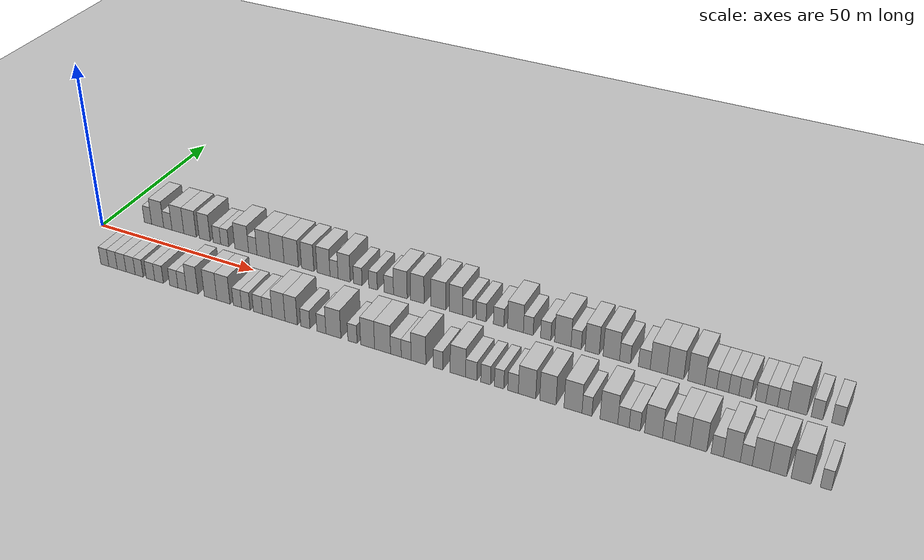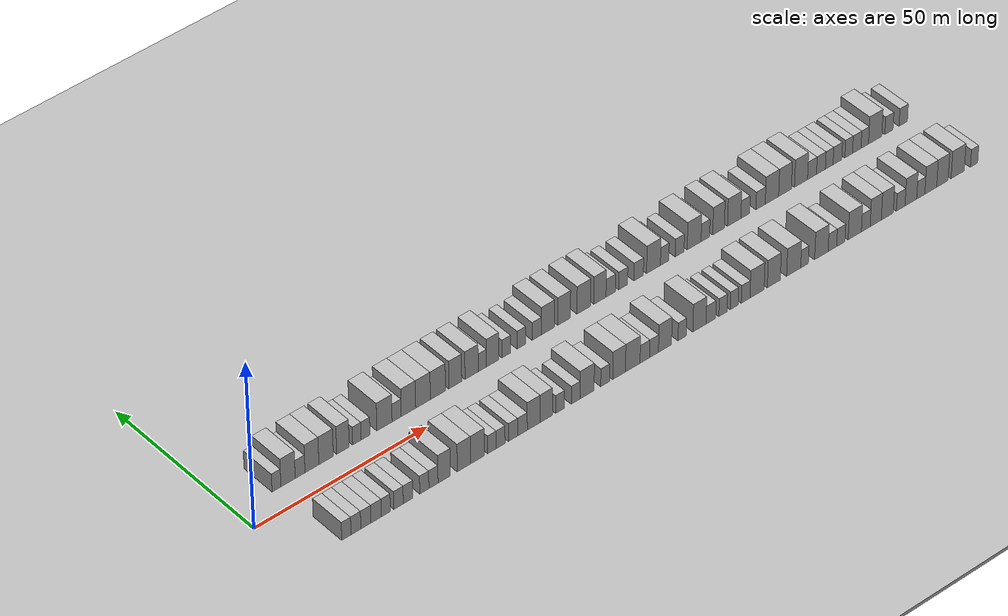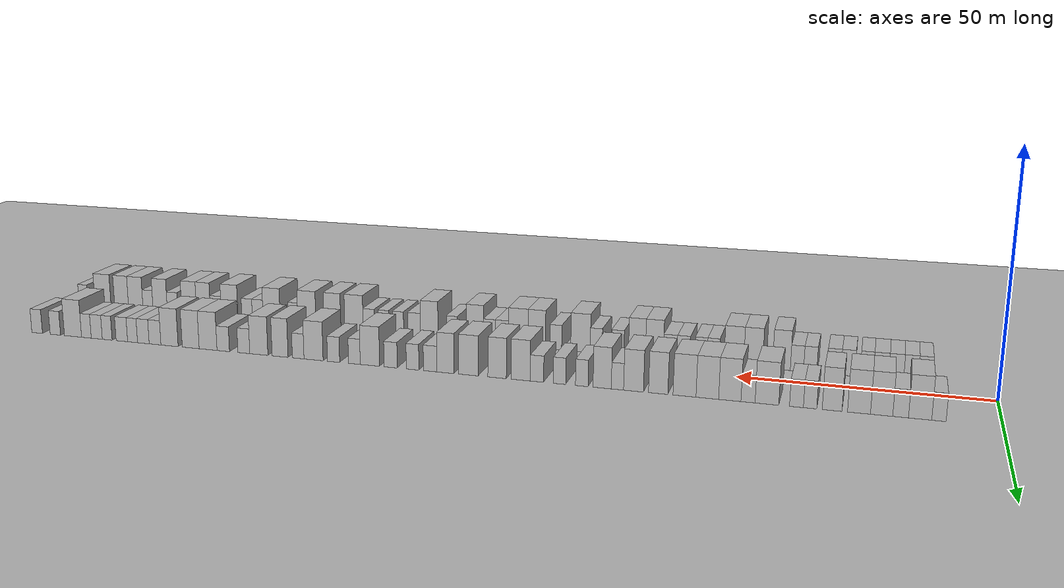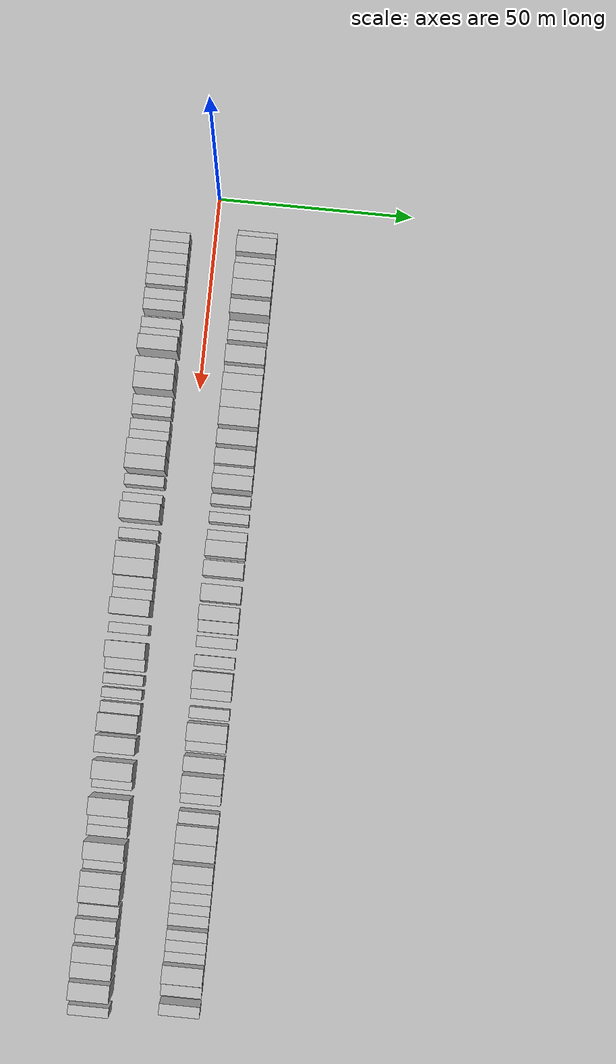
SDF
<?xml version="1.0" encoding="utf-8"?>

<sdf version="1.6">

   <world name="default">

      <gui fullscreen="0">

         <camera name="user_camera">

            <pose>-15 0 4.57585 0 0 0</pose>

            <view_controller>orbit</view_controller>

         </camera>

      </gui>

      <scene>

         <sky>

           <clouds>

             <speed>12</speed>

           </clouds>

         </sky>

         <ambient>0.4 0.4 0.4 1</ambient>

         <background>0.7 0.7 0.7 1</background>

         <shadows>1</shadows>

      </scene>

      <gravity>0 0 -9.8066</gravity>

      <magnetic_field>6e-06 2.3e-05 -4.2e-05</magnetic_field>

      <physics default="0" name="default_physics" type="ode">

         <ode>

            <solver>

               <type>quick</type>

               <iters>10</iters>

               <sor>1.0</sor>

               <use_dynamic_moi_rescaling>0</use_dynamic_moi_rescaling>

            </solver>

            <constraints>

               <cfm>0</cfm>

               <erp>0.2</erp>

               <contact_max_correcting_vel>100</contact_max_correcting_vel>

               <contact_surface_layer>0.001</contact_surface_layer>

            </constraints>

         </ode>

         <max_step_size>0.004</max_step_size>

         <real_time_factor>1</real_time_factor>

         <real_time_update_rate>250</real_time_update_rate>

      </physics>

      <light name="sun" type="directional">

         <cast_shadows>1</cast_shadows>

         <pose>0 0 10 0 0 0</pose>

         <diffuse>0.8 0.8 0.8 1</diffuse>

         <specular>0.2 0.2 0.2 1</specular>

         <attenuation>

            <range>1000</range>

            <constant>0.9</constant>

            <linear>0.01</linear>

            <quadratic>0.001</quadratic>

         </attenuation>

         <direction>-0.5 0.1 -0.9</direction>

      </light>

      <include>

         <name>ground_plane_1</name>

         <uri>model://HANNAS_ground_plane</uri>

         <pose>0 0 0  0 0 0</pose>

      </include>

      <include>

         <name>ground_plane_2</name>

         <uri>model://HANNAS_ground_plane</uri>

         <pose>100 0 0  0 0 0</pose>

      </include>

      <model name="building_1">

         <static>1</static>

         <pose frame="">11.2626 11.0000 0 0.000000 0.000000 1.570796</pose>

         <link name="link">

            <pose frame="">0 0 3.00 0 0 0</pose>

            <collision name="collision">

               <geometry>

                  <box>

                     <size>10.0000 2.5252 6.0000</size>

                  </box>

               </geometry>

               <max_contacts>10</max_contacts>

               <surface>

                  <contact>

                     <ode/>

                  </contact>

                  <bounce/>

                  <friction>

                     <torsional>

                        <ode/>

                     </torsional>

                     <ode/>

                  </friction>

               </surface>

            </collision>

            <visual name="visual">

               <cast_shadows>0</cast_shadows>

               <geometry>

                  <box>

                     <size>10.0000 2.5252 6.0000</size>

                  </box>

               </geometry>

               <material>

                  <script>

                     <uri>model://HANNAS_wall/materials/scripts</uri>

                     <uri>model://HANNAS_wall/materials/textures</uri>

                     <name>vrc/HANNAS_wall</name>

                  </script>

               </material>

            </visual>

            <self_collide>0</self_collide>

            <enable_wind>0</enable_wind>

            <kinematic>0</kinematic>

         </link>

      </model>

      <model name="building_2">

         <static>1</static>

         <pose frame="">14.5752 11.0000 0 0.000000 0.000000 1.570796</pose>

         <link name="link">

            <pose frame="">0 0 4.50 0 0 0</pose>

            <collision name="collision">

               <geometry>

                  <box>

                     <size>10.0000 4.1001 9.0000</size>

                  </box>

               </geometry>

               <max_contacts>10</max_contacts>

               <surface>

                  <contact>

                     <ode/>

                  </contact>

                  <bounce/>

                  <friction>

                     <torsional>

                        <ode/>

                     </torsional>

                     <ode/>

                  </friction>

               </surface>

            </collision>

            <visual name="visual">

               <cast_shadows>0</cast_shadows>

               <geometry>

                  <box>

                     <size>10.0000 4.1001 9.0000</size>

                  </box>

               </geometry>

               <material>

                  <script>

                     <uri>model://HANNAS_wall/materials/scripts</uri>

                     <uri>model://HANNAS_wall/materials/textures</uri>

                     <name>vrc/HANNAS_wall</name>

                  </script>

               </material>

            </visual>

            <self_collide>0</self_collide>

            <enable_wind>0</enable_wind>

            <kinematic>0</kinematic>

         </link>

      </model>

      <model name="building_3">

         <static>1</static>

         <pose frame="">18.0243 11.0000 0 0.000000 0.000000 1.570796</pose>

         <link name="link">

            <pose frame="">0 0 3.00 0 0 0</pose>

            <collision name="collision">

               <geometry>

                  <box>

                     <size>10.0000 2.7979 6.0000</size>

                  </box>

               </geometry>

               <max_contacts>10</max_contacts>

               <surface>

                  <contact>

                     <ode/>

                  </contact>

                  <bounce/>

                  <friction>

                     <torsional>

                        <ode/>

                     </torsional>

                     <ode/>

                  </friction>

               </surface>

            </collision>

            <visual name="visual">

               <cast_shadows>0</cast_shadows>

               <geometry>

                  <box>

                     <size>10.0000 2.7979 6.0000</size>

                  </box>

               </geometry>

               <material>

                  <script>

                     <uri>model://HANNAS_wall/materials/scripts</uri>

                     <uri>model://HANNAS_wall/materials/textures</uri>

                     <name>vrc/HANNAS_wall</name>

                  </script>

               </material>

            </visual>

            <self_collide>0</self_collide>

            <enable_wind>0</enable_wind>

            <kinematic>0</kinematic>

         </link>

      </model>

      <model name="building_4">

         <static>1</static>

         <pose frame="">21.4172 11.0000 0 0.000000 0.000000 1.570796</pose>

         <link name="link">

            <pose frame="">0 0 4.50 0 0 0</pose>

            <collision name="collision">

               <geometry>

                  <box>

                     <size>10.0000 3.9879 9.0000</size>

                  </box>

               </geometry>

               <max_contacts>10</max_contacts>

               <surface>

                  <contact>

                     <ode/>

                  </contact>

                  <bounce/>

                  <friction>

                     <torsional>

                        <ode/>

                     </torsional>

                     <ode/>

                  </friction>

               </surface>

            </collision>

            <visual name="visual">

               <cast_shadows>0</cast_shadows>

               <geometry>

                  <box>

                     <size>10.0000 3.9879 9.0000</size>

                  </box>

               </geometry>

               <material>

                  <script>

                     <uri>model://HANNAS_wall/materials/scripts</uri>

                     <uri>model://HANNAS_wall/materials/textures</uri>

                     <name>vrc/HANNAS_wall</name>

                  </script>

               </material>

            </visual>

            <self_collide>0</self_collide>

            <enable_wind>0</enable_wind>

            <kinematic>0</kinematic>

         </link>

      </model>

      <model name="building_5">

         <static>1</static>

         <pose frame="">25.4855 11.0000 0 0.000000 0.000000 1.570796</pose>

         <link name="link">

            <pose frame="">0 0 4.50 0 0 0</pose>

            <collision name="collision">

               <geometry>

                  <box>

                     <size>10.0000 4.1488 9.0000</size>

                  </box>

               </geometry>

               <max_contacts>10</max_contacts>

               <surface>

                  <contact>

                     <ode/>

                  </contact>

                  <bounce/>

                  <friction>

                     <torsional>

                        <ode/>

                     </torsional>

                     <ode/>

                  </friction>

               </surface>

            </collision>

            <visual name="visual">

               <cast_shadows>0</cast_shadows>

               <geometry>

                  <box>

                     <size>10.0000 4.1488 9.0000</size>

                  </box>

               </geometry>

               <material>

                  <script>

                     <uri>model://HANNAS_wall/materials/scripts</uri>

                     <uri>model://HANNAS_wall/materials/textures</uri>

                     <name>vrc/HANNAS_wall</name>

                  </script>

               </material>

            </visual>

            <self_collide>0</self_collide>

            <enable_wind>0</enable_wind>

            <kinematic>0</kinematic>

         </link>

      </model>

      <model name="building_6">

         <static>1</static>

         <pose frame="">30.3708 11.0000 0 0.000000 0.000000 1.570796</pose>

         <link name="link">

            <pose frame="">0 0 4.50 0 0 0</pose>

            <collision name="collision">

               <geometry>

                  <box>

                     <size>10.0000 3.6217 9.0000</size>

                  </box>

               </geometry>

               <max_contacts>10</max_contacts>

               <surface>

                  <contact>

                     <ode/>

                  </contact>

                  <bounce/>

                  <friction>

                     <torsional>

                        <ode/>

                     </torsional>

                     <ode/>

                  </friction>

               </surface>

            </collision>

            <visual name="visual">

               <cast_shadows>0</cast_shadows>

               <geometry>

                  <box>

                     <size>10.0000 3.6217 9.0000</size>

                  </box>

               </geometry>

               <material>

                  <script>

                     <uri>model://HANNAS_wall/materials/scripts</uri>

                     <uri>model://HANNAS_wall/materials/textures</uri>

                     <name>vrc/HANNAS_wall</name>

                  </script>

               </material>

            </visual>

            <self_collide>0</self_collide>

            <enable_wind>0</enable_wind>

            <kinematic>0</kinematic>

         </link>

      </model>

      <model name="building_7">

         <static>1</static>

         <pose frame="">34.4124 11.0000 0 0.000000 0.000000 1.570796</pose>

         <link name="link">

            <pose frame="">0 0 3.00 0 0 0</pose>

            <collision name="collision">

               <geometry>

                  <box>

                     <size>10.0000 2.4615 6.0000</size>

                  </box>

               </geometry>

               <max_contacts>10</max_contacts>

               <surface>

                  <contact>

                     <ode/>

                  </contact>

                  <bounce/>

                  <friction>

                     <torsional>

                        <ode/>

                     </torsional>

                     <ode/>

                  </friction>

               </surface>

            </collision>

            <visual name="visual">

               <cast_shadows>0</cast_shadows>

               <geometry>

                  <box>

                     <size>10.0000 2.4615 6.0000</size>

                  </box>

               </geometry>

               <material>

                  <script>

                     <uri>model://HANNAS_wall/materials/scripts</uri>

                     <uri>model://HANNAS_wall/materials/textures</uri>

                     <name>vrc/HANNAS_wall</name>

                  </script>

               </material>

            </visual>

            <self_collide>0</self_collide>

            <enable_wind>0</enable_wind>

            <kinematic>0</kinematic>

         </link>

      </model>

      <model name="building_8">

         <static>1</static>

         <pose frame="">36.9330 11.0000 0 0.000000 0.000000 1.570796</pose>

         <link name="link">

            <pose frame="">0 0 3.00 0 0 0</pose>

            <collision name="collision">

               <geometry>

                  <box>

                     <size>10.0000 2.5796 6.0000</size>

                  </box>

               </geometry>

               <max_contacts>10</max_contacts>

               <surface>

                  <contact>

                     <ode/>

                  </contact>

                  <bounce/>

                  <friction>

                     <torsional>

                        <ode/>

                     </torsional>

                     <ode/>

                  </friction>

               </surface>

            </collision>

            <visual name="visual">

               <cast_shadows>0</cast_shadows>

               <geometry>

                  <box>

                     <size>10.0000 2.5796 6.0000</size>

                  </box>

               </geometry>

               <material>

                  <script>

                     <uri>model://HANNAS_wall/materials/scripts</uri>

                     <uri>model://HANNAS_wall/materials/textures</uri>

                     <name>vrc/HANNAS_wall</name>

                  </script>

               </material>

            </visual>

            <self_collide>0</self_collide>

            <enable_wind>0</enable_wind>

            <kinematic>0</kinematic>

         </link>

      </model>

      <model name="building_9">

         <static>1</static>

         <pose frame="">42.4474 11.0000 0 0.000000 0.000000 1.570796</pose>

         <link name="link">

            <pose frame="">0 0 4.50 0 0 0</pose>

            <collision name="collision">

               <geometry>

                  <box>

                     <size>10.0000 4.4493 9.0000</size>

                  </box>

               </geometry>

               <max_contacts>10</max_contacts>

               <surface>

                  <contact>

                     <ode/>

                  </contact>

                  <bounce/>

                  <friction>

                     <torsional>

                        <ode/>

                     </torsional>

                     <ode/>

                  </friction>

               </surface>

            </collision>

            <visual name="visual">

               <cast_shadows>0</cast_shadows>

               <geometry>

                  <box>

                     <size>10.0000 4.4493 9.0000</size>

                  </box>

               </geometry>

               <material>

                  <script>

                     <uri>model://HANNAS_wall/materials/scripts</uri>

                     <uri>model://HANNAS_wall/materials/textures</uri>

                     <name>vrc/HANNAS_wall</name>

                  </script>

               </material>

            </visual>

            <self_collide>0</self_collide>

            <enable_wind>0</enable_wind>

            <kinematic>0</kinematic>

         </link>

      </model>

      <model name="building_10">

         <static>1</static>

         <pose frame="">46.0073 11.0000 0 0.000000 0.000000 1.570796</pose>

         <link name="link">

            <pose frame="">0 0 3.00 0 0 0</pose>

            <collision name="collision">

               <geometry>

                  <box>

                     <size>10.0000 2.6704 6.0000</size>

                  </box>

               </geometry>

               <max_contacts>10</max_contacts>

               <surface>

                  <contact>

                     <ode/>

                  </contact>

                  <bounce/>

                  <friction>

                     <torsional>

                        <ode/>

                     </torsional>

                     <ode/>

                  </friction>

               </surface>

            </collision>

            <visual name="visual">

               <cast_shadows>0</cast_shadows>

               <geometry>

                  <box>

                     <size>10.0000 2.6704 6.0000</size>

                  </box>

               </geometry>

               <material>

                  <script>

                     <uri>model://HANNAS_wall/materials/scripts</uri>

                     <uri>model://HANNAS_wall/materials/textures</uri>

                     <name>vrc/HANNAS_wall</name>

                  </script>

               </material>

            </visual>

            <self_collide>0</self_collide>

            <enable_wind>0</enable_wind>

            <kinematic>0</kinematic>

         </link>

      </model>

      <model name="building_11">

         <static>1</static>

         <pose frame="">49.4722 11.0000 0 0.000000 0.000000 1.570796</pose>

         <link name="link">

            <pose frame="">0 0 4.50 0 0 0</pose>

            <collision name="collision">

               <geometry>

                  <box>

                     <size>10.0000 4.2595 9.0000</size>

                  </box>

               </geometry>

               <max_contacts>10</max_contacts>

               <surface>

                  <contact>

                     <ode/>

                  </contact>

                  <bounce/>

                  <friction>

                     <torsional>

                        <ode/>

                     </torsional>

                     <ode/>

                  </friction>

               </surface>

            </collision>

            <visual name="visual">

               <cast_shadows>0</cast_shadows>

               <geometry>

                  <box>

                     <size>10.0000 4.2595 9.0000</size>

                  </box>

               </geometry>

               <material>

                  <script>

                     <uri>model://HANNAS_wall/materials/scripts</uri>

                     <uri>model://HANNAS_wall/materials/textures</uri>

                     <name>vrc/HANNAS_wall</name>

                  </script>

               </material>

            </visual>

            <self_collide>0</self_collide>

            <enable_wind>0</enable_wind>

            <kinematic>0</kinematic>

         </link>

      </model>

      <model name="building_12">

         <static>1</static>

         <pose frame="">53.7757 11.0000 0 0.000000 0.000000 1.570796</pose>

         <link name="link">

            <pose frame="">0 0 4.50 0 0 0</pose>

            <collision name="collision">

               <geometry>

                  <box>

                     <size>10.0000 4.3475 9.0000</size>

                  </box>

               </geometry>

               <max_contacts>10</max_contacts>

               <surface>

                  <contact>

                     <ode/>

                  </contact>

                  <bounce/>

                  <friction>

                     <torsional>

                        <ode/>

                     </torsional>

                     <ode/>

                  </friction>

               </surface>

            </collision>

            <visual name="visual">

               <cast_shadows>0</cast_shadows>

               <geometry>

                  <box>

                     <size>10.0000 4.3475 9.0000</size>

                  </box>

               </geometry>

               <material>

                  <script>

                     <uri>model://HANNAS_wall/materials/scripts</uri>

                     <uri>model://HANNAS_wall/materials/textures</uri>

                     <name>vrc/HANNAS_wall</name>

                  </script>

               </material>

            </visual>

            <self_collide>0</self_collide>

            <enable_wind>0</enable_wind>

            <kinematic>0</kinematic>

         </link>

      </model>

      <model name="building_13">

         <static>1</static>

         <pose frame="">58.1860 11.0000 0 0.000000 0.000000 1.570796</pose>

         <link name="link">

            <pose frame="">0 0 4.50 0 0 0</pose>

            <collision name="collision">

               <geometry>

                  <box>

                     <size>10.0000 4.4731 9.0000</size>

                  </box>

               </geometry>

               <max_contacts>10</max_contacts>

               <surface>

                  <contact>

                     <ode/>

                  </contact>

                  <bounce/>

                  <friction>

                     <torsional>

                        <ode/>

                     </torsional>

                     <ode/>

                  </friction>

               </surface>

            </collision>

            <visual name="visual">

               <cast_shadows>0</cast_shadows>

               <geometry>

                  <box>

                     <size>10.0000 4.4731 9.0000</size>

                  </box>

               </geometry>

               <material>

                  <script>

                     <uri>model://HANNAS_wall/materials/scripts</uri>

                     <uri>model://HANNAS_wall/materials/textures</uri>

                     <name>vrc/HANNAS_wall</name>

                  </script>

               </material>

            </visual>

            <self_collide>0</self_collide>

            <enable_wind>0</enable_wind>

            <kinematic>0</kinematic>

         </link>

      </model>

      <model name="building_14">

         <static>1</static>

         <pose frame="">63.3259 11.0000 0 0.000000 0.000000 1.570796</pose>

         <link name="link">

            <pose frame="">0 0 4.50 0 0 0</pose>

            <collision name="collision">

               <geometry>

                  <box>

                     <size>10.0000 3.8066 9.0000</size>

                  </box>

               </geometry>

               <max_contacts>10</max_contacts>

               <surface>

                  <contact>

                     <ode/>

                  </contact>

                  <bounce/>

                  <friction>

                     <torsional>

                        <ode/>

                     </torsional>

                     <ode/>

                  </friction>

               </surface>

            </collision>

            <visual name="visual">

               <cast_shadows>0</cast_shadows>

               <geometry>

                  <box>

                     <size>10.0000 3.8066 9.0000</size>

                  </box>

               </geometry>

               <material>

                  <script>

                     <uri>model://HANNAS_wall/materials/scripts</uri>

                     <uri>model://HANNAS_wall/materials/textures</uri>

                     <name>vrc/HANNAS_wall</name>

                  </script>

               </material>

            </visual>

            <self_collide>0</self_collide>

            <enable_wind>0</enable_wind>

            <kinematic>0</kinematic>

         </link>

      </model>

      <model name="building_15">

         <static>1</static>

         <pose frame="">68.2018 11.0000 0 0.000000 0.000000 1.570796</pose>

         <link name="link">

            <pose frame="">0 0 4.50 0 0 0</pose>

            <collision name="collision">

               <geometry>

                  <box>

                     <size>10.0000 3.9451 9.0000</size>

                  </box>

               </geometry>

               <max_contacts>10</max_contacts>

               <surface>

                  <contact>

                     <ode/>

                  </contact>

                  <bounce/>

                  <friction>

                     <torsional>

                        <ode/>

                     </torsional>

                     <ode/>

                  </friction>

               </surface>

            </collision>

            <visual name="visual">

               <cast_shadows>0</cast_shadows>

               <geometry>

                  <box>

                     <size>10.0000 3.9451 9.0000</size>

                  </box>

               </geometry>

               <material>

                  <script>

                     <uri>model://HANNAS_wall/materials/scripts</uri>

                     <uri>model://HANNAS_wall/materials/textures</uri>

                     <name>vrc/HANNAS_wall</name>

                  </script>

               </material>

            </visual>

            <self_collide>0</self_collide>

            <enable_wind>0</enable_wind>

            <kinematic>0</kinematic>

         </link>

      </model>

      <model name="building_16">

         <static>1</static>

         <pose frame="">71.4081 11.0000 0 0.000000 0.000000 1.570796</pose>

         <link name="link">

            <pose frame="">0 0 3.00 0 0 0</pose>

            <collision name="collision">

               <geometry>

                  <box>

                     <size>10.0000 2.4675 6.0000</size>

                  </box>

               </geometry>

               <max_contacts>10</max_contacts>

               <surface>

                  <contact>

                     <ode/>

                  </contact>

                  <bounce/>

                  <friction>

                     <torsional>

                        <ode/>

                     </torsional>

                     <ode/>

                  </friction>

               </surface>

            </collision>

            <visual name="visual">

               <cast_shadows>0</cast_shadows>

               <geometry>

                  <box>

                     <size>10.0000 2.4675 6.0000</size>

                  </box>

               </geometry>

               <material>

                  <script>

                     <uri>model://HANNAS_wall/materials/scripts</uri>

                     <uri>model://HANNAS_wall/materials/textures</uri>

                     <name>vrc/HANNAS_wall</name>

                  </script>

               </material>

            </visual>

            <self_collide>0</self_collide>

            <enable_wind>0</enable_wind>

            <kinematic>0</kinematic>

         </link>

      </model>

      <model name="building_17">

         <static>1</static>

         <pose frame="">74.4741 11.0000 0 0.000000 0.000000 1.570796</pose>

         <link name="link">

            <pose frame="">0 0 4.50 0 0 0</pose>

            <collision name="collision">

               <geometry>

                  <box>

                     <size>10.0000 3.6646 9.0000</size>

                  </box>

               </geometry>

               <max_contacts>10</max_contacts>

               <surface>

                  <contact>

                     <ode/>

                  </contact>

                  <bounce/>

                  <friction>

                     <torsional>

                        <ode/>

                     </torsional>

                     <ode/>

                  </friction>

               </surface>

            </collision>

            <visual name="visual">

               <cast_shadows>0</cast_shadows>

               <geometry>

                  <box>

                     <size>10.0000 3.6646 9.0000</size>

                  </box>

               </geometry>

               <material>

                  <script>

                     <uri>model://HANNAS_wall/materials/scripts</uri>

                     <uri>model://HANNAS_wall/materials/textures</uri>

                     <name>vrc/HANNAS_wall</name>

                  </script>

               </material>

            </visual>

            <self_collide>0</self_collide>

            <enable_wind>0</enable_wind>

            <kinematic>0</kinematic>

         </link>

      </model>

      <model name="building_18">

         <static>1</static>

         <pose frame="">78.5879 11.0000 0 0.000000 0.000000 1.570796</pose>

         <link name="link">

            <pose frame="">0 0 3.00 0 0 0</pose>

            <collision name="collision">

               <geometry>

                  <box>

                     <size>10.0000 2.5629 6.0000</size>

                  </box>

               </geometry>

               <max_contacts>10</max_contacts>

               <surface>

                  <contact>

                     <ode/>

                  </contact>

                  <bounce/>

                  <friction>

                     <torsional>

                        <ode/>

                     </torsional>

                     <ode/>

                  </friction>

               </surface>

            </collision>

            <visual name="visual">

               <cast_shadows>0</cast_shadows>

               <geometry>

                  <box>

                     <size>10.0000 2.5629 6.0000</size>

                  </box>

               </geometry>

               <material>

                  <script>

                     <uri>model://HANNAS_wall/materials/scripts</uri>

                     <uri>model://HANNAS_wall/materials/textures</uri>

                     <name>vrc/HANNAS_wall</name>

                  </script>

               </material>

            </visual>

            <self_collide>0</self_collide>

            <enable_wind>0</enable_wind>

            <kinematic>0</kinematic>

         </link>

      </model>

      <model name="building_19">

         <static>1</static>

         <pose frame="">83.1306 11.0000 0 0.000000 0.000000 1.570796</pose>

         <link name="link">

            <pose frame="">0 0 3.00 0 0 0</pose>

            <collision name="collision">

               <geometry>

                  <box>

                     <size>10.0000 2.5227 6.0000</size>

                  </box>

               </geometry>

               <max_contacts>10</max_contacts>

               <surface>

                  <contact>

                     <ode/>

                  </contact>

                  <bounce/>

                  <friction>

                     <torsional>

                        <ode/>

                     </torsional>

                     <ode/>

                  </friction>

               </surface>

            </collision>

            <visual name="visual">

               <cast_shadows>0</cast_shadows>

               <geometry>

                  <box>

                     <size>10.0000 2.5227 6.0000</size>

                  </box>

               </geometry>

               <material>

                  <script>

                     <uri>model://HANNAS_wall/materials/scripts</uri>

                     <uri>model://HANNAS_wall/materials/textures</uri>

                     <name>vrc/HANNAS_wall</name>

                  </script>

               </material>

            </visual>

            <self_collide>0</self_collide>

            <enable_wind>0</enable_wind>

            <kinematic>0</kinematic>

         </link>

      </model>

      <model name="building_20">

         <static>1</static>

         <pose frame="">87.7749 11.0000 0 0.000000 0.000000 1.570796</pose>

         <link name="link">

            <pose frame="">0 0 3.00 0 0 0</pose>

            <collision name="collision">

               <geometry>

                  <box>

                     <size>10.0000 2.7658 6.0000</size>

                  </box>

               </geometry>

               <max_contacts>10</max_contacts>

               <surface>

                  <contact>

                     <ode/>

                  </contact>

                  <bounce/>

                  <friction>

                     <torsional>

                        <ode/>

                     </torsional>

                     <ode/>

                  </friction>

               </surface>

            </collision>

            <visual name="visual">

               <cast_shadows>0</cast_shadows>

               <geometry>

                  <box>

                     <size>10.0000 2.7658 6.0000</size>

                  </box>

               </geometry>

               <material>

                  <script>

                     <uri>model://HANNAS_wall/materials/scripts</uri>

                     <uri>model://HANNAS_wall/materials/textures</uri>

                     <name>vrc/HANNAS_wall</name>

                  </script>

               </material>

            </visual>

            <self_collide>0</self_collide>

            <enable_wind>0</enable_wind>

            <kinematic>0</kinematic>

         </link>

      </model>

      <model name="building_21">

         <static>1</static>

         <pose frame="">91.1590 11.0000 0 0.000000 0.000000 1.570796</pose>

         <link name="link">

            <pose frame="">0 0 4.50 0 0 0</pose>

            <collision name="collision">

               <geometry>

                  <box>

                     <size>10.0000 4.0024 9.0000</size>

                  </box>

               </geometry>

               <max_contacts>10</max_contacts>

               <surface>

                  <contact>

                     <ode/>

                  </contact>

                  <bounce/>

                  <friction>

                     <torsional>

                        <ode/>

                     </torsional>

                     <ode/>

                  </friction>

               </surface>

            </collision>

            <visual name="visual">

               <cast_shadows>0</cast_shadows>

               <geometry>

                  <box>

                     <size>10.0000 4.0024 9.0000</size>

                  </box>

               </geometry>

               <material>

                  <script>

                     <uri>model://HANNAS_wall/materials/scripts</uri>

                     <uri>model://HANNAS_wall/materials/textures</uri>

                     <name>vrc/HANNAS_wall</name>

                  </script>

               </material>

            </visual>

            <self_collide>0</self_collide>

            <enable_wind>0</enable_wind>

            <kinematic>0</kinematic>

         </link>

      </model>

      <model name="building_22">

         <static>1</static>

         <pose frame="">96.1032 11.0000 0 0.000000 0.000000 1.570796</pose>

         <link name="link">

            <pose frame="">0 0 4.50 0 0 0</pose>

            <collision name="collision">

               <geometry>

                  <box>

                     <size>10.0000 3.8859 9.0000</size>

                  </box>

               </geometry>

               <max_contacts>10</max_contacts>

               <surface>

                  <contact>

                     <ode/>

                  </contact>

                  <bounce/>

                  <friction>

                     <torsional>

                        <ode/>

                     </torsional>

                     <ode/>

                  </friction>

               </surface>

            </collision>

            <visual name="visual">

               <cast_shadows>0</cast_shadows>

               <geometry>

                  <box>

                     <size>10.0000 3.8859 9.0000</size>

                  </box>

               </geometry>

               <material>

                  <script>

                     <uri>model://HANNAS_wall/materials/scripts</uri>

                     <uri>model://HANNAS_wall/materials/textures</uri>

                     <name>vrc/HANNAS_wall</name>

                  </script>

               </material>

            </visual>

            <self_collide>0</self_collide>

            <enable_wind>0</enable_wind>

            <kinematic>0</kinematic>

         </link>

      </model>

      <model name="building_23">

         <static>1</static>

         <pose frame="">102.1440 11.0000 0 0.000000 0.000000 1.570796</pose>

         <link name="link">

            <pose frame="">0 0 4.50 0 0 0</pose>

            <collision name="collision">

               <geometry>

                  <box>

                     <size>10.0000 4.1956 9.0000</size>

                  </box>

               </geometry>

               <max_contacts>10</max_contacts>

               <surface>

                  <contact>

                     <ode/>

                  </contact>

                  <bounce/>

                  <friction>

                     <torsional>

                        <ode/>

                     </torsional>

                     <ode/>

                  </friction>

               </surface>

            </collision>

            <visual name="visual">

               <cast_shadows>0</cast_shadows>

               <geometry>

                  <box>

                     <size>10.0000 4.1956 9.0000</size>

                  </box>

               </geometry>

               <material>

                  <script>

                     <uri>model://HANNAS_wall/materials/scripts</uri>

                     <uri>model://HANNAS_wall/materials/textures</uri>

                     <name>vrc/HANNAS_wall</name>

                  </script>

               </material>

            </visual>

            <self_collide>0</self_collide>

            <enable_wind>0</enable_wind>

            <kinematic>0</kinematic>

         </link>

      </model>

      <model name="building_24">

         <static>1</static>

         <pose frame="">107.0892 11.0000 0 0.000000 0.000000 1.570796</pose>

         <link name="link">

            <pose frame="">0 0 4.50 0 0 0</pose>

            <collision name="collision">

               <geometry>

                  <box>

                     <size>10.0000 3.6947 9.0000</size>

                  </box>

               </geometry>

               <max_contacts>10</max_contacts>

               <surface>

                  <contact>

                     <ode/>

                  </contact>

                  <bounce/>

                  <friction>

                     <torsional>

                        <ode/>

                     </torsional>

                     <ode/>

                  </friction>

               </surface>

            </collision>

            <visual name="visual">

               <cast_shadows>0</cast_shadows>

               <geometry>

                  <box>

                     <size>10.0000 3.6947 9.0000</size>

                  </box>

               </geometry>

               <material>

                  <script>

                     <uri>model://HANNAS_wall/materials/scripts</uri>

                     <uri>model://HANNAS_wall/materials/textures</uri>

                     <name>vrc/HANNAS_wall</name>

                  </script>

               </material>

            </visual>

            <self_collide>0</self_collide>

            <enable_wind>0</enable_wind>

            <kinematic>0</kinematic>

         </link>

      </model>

      <model name="building_25">

         <static>1</static>

         <pose frame="">110.3980 11.0000 0 0.000000 0.000000 1.570796</pose>

         <link name="link">

            <pose frame="">0 0 3.00 0 0 0</pose>

            <collision name="collision">

               <geometry>

                  <box>

                     <size>10.0000 2.9231 6.0000</size>

                  </box>

               </geometry>

               <max_contacts>10</max_contacts>

               <surface>

                  <contact>

                     <ode/>

                  </contact>

                  <bounce/>

                  <friction>

                     <torsional>

                        <ode/>

                     </torsional>

                     <ode/>

                  </friction>

               </surface>

            </collision>

            <visual name="visual">

               <cast_shadows>0</cast_shadows>

               <geometry>

                  <box>

                     <size>10.0000 2.9231 6.0000</size>

                  </box>

               </geometry>

               <material>

                  <script>

                     <uri>model://HANNAS_wall/materials/scripts</uri>

                     <uri>model://HANNAS_wall/materials/textures</uri>

                     <name>vrc/HANNAS_wall</name>

                  </script>

               </material>

            </visual>

            <self_collide>0</self_collide>

            <enable_wind>0</enable_wind>

            <kinematic>0</kinematic>

         </link>

      </model>

      <model name="building_26">

         <static>1</static>

         <pose frame="">114.2277 11.0000 0 0.000000 0.000000 1.570796</pose>

         <link name="link">

            <pose frame="">0 0 3.00 0 0 0</pose>

            <collision name="collision">

               <geometry>

                  <box>

                     <size>10.0000 2.7362 6.0000</size>

                  </box>

               </geometry>

               <max_contacts>10</max_contacts>

               <surface>

                  <contact>

                     <ode/>

                  </contact>

                  <bounce/>

                  <friction>

                     <torsional>

                        <ode/>

                     </torsional>

                     <ode/>

                  </friction>

               </surface>

            </collision>

            <visual name="visual">

               <cast_shadows>0</cast_shadows>

               <geometry>

                  <box>

                     <size>10.0000 2.7362 6.0000</size>

                  </box>

               </geometry>

               <material>

                  <script>

                     <uri>model://HANNAS_wall/materials/scripts</uri>

                     <uri>model://HANNAS_wall/materials/textures</uri>

                     <name>vrc/HANNAS_wall</name>

                  </script>

               </material>

            </visual>

            <self_collide>0</self_collide>

            <enable_wind>0</enable_wind>

            <kinematic>0</kinematic>

         </link>

      </model>

      <model name="building_27">

         <static>1</static>

         <pose frame="">119.0449 11.0000 0 0.000000 0.000000 1.570796</pose>

         <link name="link">

            <pose frame="">0 0 3.00 0 0 0</pose>

            <collision name="collision">

               <geometry>

                  <box>

                     <size>10.0000 2.8983 6.0000</size>

                  </box>

               </geometry>

               <max_contacts>10</max_contacts>

               <surface>

                  <contact>

                     <ode/>

                  </contact>

                  <bounce/>

                  <friction>

                     <torsional>

                        <ode/>

                     </torsional>

                     <ode/>

                  </friction>

               </surface>

            </collision>

            <visual name="visual">

               <cast_shadows>0</cast_shadows>

               <geometry>

                  <box>

                     <size>10.0000 2.8983 6.0000</size>

                  </box>

               </geometry>

               <material>

                  <script>

                     <uri>model://HANNAS_wall/materials/scripts</uri>

                     <uri>model://HANNAS_wall/materials/textures</uri>

                     <name>vrc/HANNAS_wall</name>

                  </script>

               </material>

            </visual>

            <self_collide>0</self_collide>

            <enable_wind>0</enable_wind>

            <kinematic>0</kinematic>

         </link>

      </model>

      <model name="building_28">

         <static>1</static>

         <pose frame="">123.6505 11.0000 0 0.000000 0.000000 1.570796</pose>

         <link name="link">

            <pose frame="">0 0 4.50 0 0 0</pose>

            <collision name="collision">

               <geometry>

                  <box>

                     <size>10.0000 4.3128 9.0000</size>

                  </box>

               </geometry>

               <max_contacts>10</max_contacts>

               <surface>

                  <contact>

                     <ode/>

                  </contact>

                  <bounce/>

                  <friction>

                     <torsional>

                        <ode/>

                     </torsional>

                     <ode/>

                  </friction>

               </surface>

            </collision>

            <visual name="visual">

               <cast_shadows>0</cast_shadows>

               <geometry>

                  <box>

                     <size>10.0000 4.3128 9.0000</size>

                  </box>

               </geometry>

               <material>

                  <script>

                     <uri>model://HANNAS_wall/materials/scripts</uri>

                     <uri>model://HANNAS_wall/materials/textures</uri>

                     <name>vrc/HANNAS_wall</name>

                  </script>

               </material>

            </visual>

            <self_collide>0</self_collide>

            <enable_wind>0</enable_wind>

            <kinematic>0</kinematic>

         </link>

      </model>

      <model name="building_29">

         <static>1</static>

         <pose frame="">127.1187 11.0000 0 0.000000 0.000000 1.570796</pose>

         <link name="link">

            <pose frame="">0 0 3.00 0 0 0</pose>

            <collision name="collision">

               <geometry>

                  <box>

                     <size>10.0000 2.6236 6.0000</size>

                  </box>

               </geometry>

               <max_contacts>10</max_contacts>

               <surface>

                  <contact>

                     <ode/>

                  </contact>

                  <bounce/>

                  <friction>

                     <torsional>

                        <ode/>

                     </torsional>

                     <ode/>

                  </friction>

               </surface>

            </collision>

            <visual name="visual">

               <cast_shadows>0</cast_shadows>

               <geometry>

                  <box>

                     <size>10.0000 2.6236 6.0000</size>

                  </box>

               </geometry>

               <material>

                  <script>

                     <uri>model://HANNAS_wall/materials/scripts</uri>

                     <uri>model://HANNAS_wall/materials/textures</uri>

                     <name>vrc/HANNAS_wall</name>

                  </script>

               </material>

            </visual>

            <self_collide>0</self_collide>

            <enable_wind>0</enable_wind>

            <kinematic>0</kinematic>

         </link>

      </model>

      <model name="building_30">

         <static>1</static>

         <pose frame="">131.8054 11.0000 0 0.000000 0.000000 1.570796</pose>

         <link name="link">

            <pose frame="">0 0 3.00 0 0 0</pose>

            <collision name="collision">

               <geometry>

                  <box>

                     <size>10.0000 2.7496 6.0000</size>

                  </box>

               </geometry>

               <max_contacts>10</max_contacts>

               <surface>

                  <contact>

                     <ode/>

                  </contact>

                  <bounce/>

                  <friction>

                     <torsional>

                        <ode/>

                     </torsional>

                     <ode/>

                  </friction>

               </surface>

            </collision>

            <visual name="visual">

               <cast_shadows>0</cast_shadows>

               <geometry>

                  <box>

                     <size>10.0000 2.7496 6.0000</size>

                  </box>

               </geometry>

               <material>

                  <script>

                     <uri>model://HANNAS_wall/materials/scripts</uri>

                     <uri>model://HANNAS_wall/materials/textures</uri>

                     <name>vrc/HANNAS_wall</name>

                  </script>

               </material>

            </visual>

            <self_collide>0</self_collide>

            <enable_wind>0</enable_wind>

            <kinematic>0</kinematic>

         </link>

      </model>

      <model name="building_31">

         <static>1</static>

         <pose frame="">136.3638 11.0000 0 0.000000 0.000000 1.570796</pose>

         <link name="link">

            <pose frame="">0 0 4.50 0 0 0</pose>

            <collision name="collision">

               <geometry>

                  <box>

                     <size>10.0000 4.3673 9.0000</size>

                  </box>

               </geometry>

               <max_contacts>10</max_contacts>

               <surface>

                  <contact>

                     <ode/>

                  </contact>

                  <bounce/>

                  <friction>

                     <torsional>

                        <ode/>

                     </torsional>

                     <ode/>

                  </friction>

               </surface>

            </collision>

            <visual name="visual">

               <cast_shadows>0</cast_shadows>

               <geometry>

                  <box>

                     <size>10.0000 4.3673 9.0000</size>

                  </box>

               </geometry>

               <material>

                  <script>

                     <uri>model://HANNAS_wall/materials/scripts</uri>

                     <uri>model://HANNAS_wall/materials/textures</uri>

                     <name>vrc/HANNAS_wall</name>

                  </script>

               </material>

            </visual>

            <self_collide>0</self_collide>

            <enable_wind>0</enable_wind>

            <kinematic>0</kinematic>

         </link>

      </model>

      <model name="building_32">

         <static>1</static>

         <pose frame="">139.8839 11.0000 0 0.000000 0.000000 1.570796</pose>

         <link name="link">

            <pose frame="">0 0 3.00 0 0 0</pose>

            <collision name="collision">

               <geometry>

                  <box>

                     <size>10.0000 2.6727 6.0000</size>

                  </box>

               </geometry>

               <max_contacts>10</max_contacts>

               <surface>

                  <contact>

                     <ode/>

                  </contact>

                  <bounce/>

                  <friction>

                     <torsional>

                        <ode/>

                     </torsional>

                     <ode/>

                  </friction>

               </surface>

            </collision>

            <visual name="visual">

               <cast_shadows>0</cast_shadows>

               <geometry>

                  <box>

                     <size>10.0000 2.6727 6.0000</size>

                  </box>

               </geometry>

               <material>

                  <script>

                     <uri>model://HANNAS_wall/materials/scripts</uri>

                     <uri>model://HANNAS_wall/materials/textures</uri>

                     <name>vrc/HANNAS_wall</name>

                  </script>

               </material>

            </visual>

            <self_collide>0</self_collide>

            <enable_wind>0</enable_wind>

            <kinematic>0</kinematic>

         </link>

      </model>

      <model name="building_33">

         <static>1</static>

         <pose frame="">144.0669 11.0000 0 0.000000 0.000000 1.570796</pose>

         <link name="link">

            <pose frame="">0 0 4.50 0 0 0</pose>

            <collision name="collision">

               <geometry>

                  <box>

                     <size>10.0000 3.6934 9.0000</size>

                  </box>

               </geometry>

               <max_contacts>10</max_contacts>

               <surface>

                  <contact>

                     <ode/>

                  </contact>

                  <bounce/>

                  <friction>

                     <torsional>

                        <ode/>

                     </torsional>

                     <ode/>

                  </friction>

               </surface>

            </collision>

            <visual name="visual">

               <cast_shadows>0</cast_shadows>

               <geometry>

                  <box>

                     <size>10.0000 3.6934 9.0000</size>

                  </box>

               </geometry>

               <material>

                  <script>

                     <uri>model://HANNAS_wall/materials/scripts</uri>

                     <uri>model://HANNAS_wall/materials/textures</uri>

                     <name>vrc/HANNAS_wall</name>

                  </script>

               </material>

            </visual>

            <self_collide>0</self_collide>

            <enable_wind>0</enable_wind>

            <kinematic>0</kinematic>

         </link>

      </model>

      <model name="building_34">

         <static>1</static>

         <pose frame="">149.0356 11.0000 0 0.000000 0.000000 1.570796</pose>

         <link name="link">

            <pose frame="">0 0 4.50 0 0 0</pose>

            <collision name="collision">

               <geometry>

                  <box>

                     <size>10.0000 4.2439 9.0000</size>

                  </box>

               </geometry>

               <max_contacts>10</max_contacts>

               <surface>

                  <contact>

                     <ode/>

                  </contact>

                  <bounce/>

                  <friction>

                     <torsional>

                        <ode/>

                     </torsional>

                     <ode/>

                  </friction>

               </surface>

            </collision>

            <visual name="visual">

               <cast_shadows>0</cast_shadows>

               <geometry>

                  <box>

                     <size>10.0000 4.2439 9.0000</size>

                  </box>

               </geometry>

               <material>

                  <script>

                     <uri>model://HANNAS_wall/materials/scripts</uri>

                     <uri>model://HANNAS_wall/materials/textures</uri>

                     <name>vrc/HANNAS_wall</name>

                  </script>

               </material>

            </visual>

            <self_collide>0</self_collide>

            <enable_wind>0</enable_wind>

            <kinematic>0</kinematic>

         </link>

      </model>

      <model name="building_35">

         <static>1</static>

         <pose frame="">152.5553 11.0000 0 0.000000 0.000000 1.570796</pose>

         <link name="link">

            <pose frame="">0 0 3.00 0 0 0</pose>

            <collision name="collision">

               <geometry>

                  <box>

                     <size>10.0000 2.7955 6.0000</size>

                  </box>

               </geometry>

               <max_contacts>10</max_contacts>

               <surface>

                  <contact>

                     <ode/>

                  </contact>

                  <bounce/>

                  <friction>

                     <torsional>

                        <ode/>

                     </torsional>

                     <ode/>

                  </friction>

               </surface>

            </collision>

            <visual name="visual">

               <cast_shadows>0</cast_shadows>

               <geometry>

                  <box>

                     <size>10.0000 2.7955 6.0000</size>

                  </box>

               </geometry>

               <material>

                  <script>

                     <uri>model://HANNAS_wall/materials/scripts</uri>

                     <uri>model://HANNAS_wall/materials/textures</uri>

                     <name>vrc/HANNAS_wall</name>

                  </script>

               </material>

            </visual>

            <self_collide>0</self_collide>

            <enable_wind>0</enable_wind>

            <kinematic>0</kinematic>

         </link>

      </model>

      <model name="building_36">

         <static>1</static>

         <pose frame="">157.4433 11.0000 0 0.000000 0.000000 1.570796</pose>

         <link name="link">

            <pose frame="">0 0 3.00 0 0 0</pose>

            <collision name="collision">

               <geometry>

                  <box>

                     <size>10.0000 2.9805 6.0000</size>

                  </box>

               </geometry>

               <max_contacts>10</max_contacts>

               <surface>

                  <contact>

                     <ode/>

                  </contact>

                  <bounce/>

                  <friction>

                     <torsional>

                        <ode/>

                     </torsional>

                     <ode/>

                  </friction>

               </surface>

            </collision>

            <visual name="visual">

               <cast_shadows>0</cast_shadows>

               <geometry>

                  <box>

                     <size>10.0000 2.9805 6.0000</size>

                  </box>

               </geometry>

               <material>

                  <script>

                     <uri>model://HANNAS_wall/materials/scripts</uri>

                     <uri>model://HANNAS_wall/materials/textures</uri>

                     <name>vrc/HANNAS_wall</name>

                  </script>

               </material>

            </visual>

            <self_collide>0</self_collide>

            <enable_wind>0</enable_wind>

            <kinematic>0</kinematic>

         </link>

      </model>

      <model name="building_37">

         <static>1</static>

         <pose frame="">161.0737 11.0000 0 0.000000 0.000000 1.570796</pose>

         <link name="link">

            <pose frame="">0 0 4.50 0 0 0</pose>

            <collision name="collision">

               <geometry>

                  <box>

                     <size>10.0000 4.2805 9.0000</size>

                  </box>

               </geometry>

               <max_contacts>10</max_contacts>

               <surface>

                  <contact>

                     <ode/>

                  </contact>

                  <bounce/>

                  <friction>

                     <torsional>

                        <ode/>

                     </torsional>

                     <ode/>

                  </friction>

               </surface>

            </collision>

            <visual name="visual">

               <cast_shadows>0</cast_shadows>

               <geometry>

                  <box>

                     <size>10.0000 4.2805 9.0000</size>

                  </box>

               </geometry>

               <material>

                  <script>

                     <uri>model://HANNAS_wall/materials/scripts</uri>

                     <uri>model://HANNAS_wall/materials/textures</uri>

                     <name>vrc/HANNAS_wall</name>

                  </script>

               </material>

            </visual>

            <self_collide>0</self_collide>

            <enable_wind>0</enable_wind>

            <kinematic>0</kinematic>

         </link>

      </model>

      <model name="building_38">

         <static>1</static>

         <pose frame="">165.2589 11.0000 0 0.000000 0.000000 1.570796</pose>

         <link name="link">

            <pose frame="">0 0 4.50 0 0 0</pose>

            <collision name="collision">

               <geometry>

                  <box>

                     <size>10.0000 4.0900 9.0000</size>

                  </box>

               </geometry>

               <max_contacts>10</max_contacts>

               <surface>

                  <contact>

                     <ode/>

                  </contact>

                  <bounce/>

                  <friction>

                     <torsional>

                        <ode/>

                     </torsional>

                     <ode/>

                  </friction>

               </surface>

            </collision>

            <visual name="visual">

               <cast_shadows>0</cast_shadows>

               <geometry>

                  <box>

                     <size>10.0000 4.0900 9.0000</size>

                  </box>

               </geometry>

               <material>

                  <script>

                     <uri>model://HANNAS_wall/materials/scripts</uri>

                     <uri>model://HANNAS_wall/materials/textures</uri>

                     <name>vrc/HANNAS_wall</name>

                  </script>

               </material>

            </visual>

            <self_collide>0</self_collide>

            <enable_wind>0</enable_wind>

            <kinematic>0</kinematic>

         </link>

      </model>

      <model name="building_39">

         <static>1</static>

         <pose frame="">170.4120 11.0000 0 0.000000 0.000000 1.570796</pose>

         <link name="link">

            <pose frame="">0 0 4.50 0 0 0</pose>

            <collision name="collision">

               <geometry>

                  <box>

                     <size>10.0000 4.2162 9.0000</size>

                  </box>

               </geometry>

               <max_contacts>10</max_contacts>

               <surface>

                  <contact>

                     <ode/>

                  </contact>

                  <bounce/>

                  <friction>

                     <torsional>

                        <ode/>

                     </torsional>

                     <ode/>

                  </friction>

               </surface>

            </collision>

            <visual name="visual">

               <cast_shadows>0</cast_shadows>

               <geometry>

                  <box>

                     <size>10.0000 4.2162 9.0000</size>

                  </box>

               </geometry>

               <material>

                  <script>

                     <uri>model://HANNAS_wall/materials/scripts</uri>

                     <uri>model://HANNAS_wall/materials/textures</uri>

                     <name>vrc/HANNAS_wall</name>

                  </script>

               </material>

            </visual>

            <self_collide>0</self_collide>

            <enable_wind>0</enable_wind>

            <kinematic>0</kinematic>

         </link>

      </model>

      <model name="building_40">

         <static>1</static>

         <pose frame="">173.9680 11.0000 0 0.000000 0.000000 1.570796</pose>

         <link name="link">

            <pose frame="">0 0 3.00 0 0 0</pose>

            <collision name="collision">

               <geometry>

                  <box>

                     <size>10.0000 2.8957 6.0000</size>

                  </box>

               </geometry>

               <max_contacts>10</max_contacts>

               <surface>

                  <contact>

                     <ode/>

                  </contact>

                  <bounce/>

                  <friction>

                     <torsional>

                        <ode/>

                     </torsional>

                     <ode/>

                  </friction>

               </surface>

            </collision>

            <visual name="visual">

               <cast_shadows>0</cast_shadows>

               <geometry>

                  <box>

                     <size>10.0000 2.8957 6.0000</size>

                  </box>

               </geometry>

               <material>

                  <script>

                     <uri>model://HANNAS_wall/materials/scripts</uri>

                     <uri>model://HANNAS_wall/materials/textures</uri>

                     <name>vrc/HANNAS_wall</name>

                  </script>

               </material>

            </visual>

            <self_collide>0</self_collide>

            <enable_wind>0</enable_wind>

            <kinematic>0</kinematic>

         </link>

      </model>

      <model name="building_41">

         <static>1</static>

         <pose frame="">176.8570 11.0000 0 0.000000 0.000000 1.570796</pose>

         <link name="link">

            <pose frame="">0 0 3.00 0 0 0</pose>

            <collision name="collision">

               <geometry>

                  <box>

                     <size>10.0000 2.8822 6.0000</size>

                  </box>

               </geometry>

               <max_contacts>10</max_contacts>

               <surface>

                  <contact>

                     <ode/>

                  </contact>

                  <bounce/>

                  <friction>

                     <torsional>

                        <ode/>

                     </torsional>

                     <ode/>

                  </friction>

               </surface>

            </collision>

            <visual name="visual">

               <cast_shadows>0</cast_shadows>

               <geometry>

                  <box>

                     <size>10.0000 2.8822 6.0000</size>

                  </box>

               </geometry>

               <material>

                  <script>

                     <uri>model://HANNAS_wall/materials/scripts</uri>

                     <uri>model://HANNAS_wall/materials/textures</uri>

                     <name>vrc/HANNAS_wall</name>

                  </script>

               </material>

            </visual>

            <self_collide>0</self_collide>

            <enable_wind>0</enable_wind>

            <kinematic>0</kinematic>

         </link>

      </model>

      <model name="building_42">

         <static>1</static>

         <pose frame="">179.5350 11.0000 0 0.000000 0.000000 1.570796</pose>

         <link name="link">

            <pose frame="">0 0 3.00 0 0 0</pose>

            <collision name="collision">

               <geometry>

                  <box>

                     <size>10.0000 2.4739 6.0000</size>

                  </box>

               </geometry>

               <max_contacts>10</max_contacts>

               <surface>

                  <contact>

                     <ode/>

                  </contact>

                  <bounce/>

                  <friction>

                     <torsional>

                        <ode/>

                     </torsional>

                     <ode/>

                  </friction>

               </surface>

            </collision>

            <visual name="visual">

               <cast_shadows>0</cast_shadows>

               <geometry>

                  <box>

                     <size>10.0000 2.4739 6.0000</size>

                  </box>

               </geometry>

               <material>

                  <script>

                     <uri>model://HANNAS_wall/materials/scripts</uri>

                     <uri>model://HANNAS_wall/materials/textures</uri>

                     <name>vrc/HANNAS_wall</name>

                  </script>

               </material>

            </visual>

            <self_collide>0</self_collide>

            <enable_wind>0</enable_wind>

            <kinematic>0</kinematic>

         </link>

      </model>

      <model name="building_43">

         <static>1</static>

         <pose frame="">182.2047 11.0000 0 0.000000 0.000000 1.570796</pose>

         <link name="link">

            <pose frame="">0 0 3.00 0 0 0</pose>

            <collision name="collision">

               <geometry>

                  <box>

                     <size>10.0000 2.8656 6.0000</size>

                  </box>

               </geometry>

               <max_contacts>10</max_contacts>

               <surface>

                  <contact>

                     <ode/>

                  </contact>

                  <bounce/>

                  <friction>

                     <torsional>

                        <ode/>

                     </torsional>

                     <ode/>

                  </friction>

               </surface>

            </collision>

            <visual name="visual">

               <cast_shadows>0</cast_shadows>

               <geometry>

                  <box>

                     <size>10.0000 2.8656 6.0000</size>

                  </box>

               </geometry>

               <material>

                  <script>

                     <uri>model://HANNAS_wall/materials/scripts</uri>

                     <uri>model://HANNAS_wall/materials/textures</uri>

                     <name>vrc/HANNAS_wall</name>

                  </script>

               </material>

            </visual>

            <self_collide>0</self_collide>

            <enable_wind>0</enable_wind>

            <kinematic>0</kinematic>

         </link>

      </model>

      <model name="building_44">

         <static>1</static>

         <pose frame="">185.8760 11.0000 0 0.000000 0.000000 1.570796</pose>

         <link name="link">

            <pose frame="">0 0 3.00 0 0 0</pose>

            <collision name="collision">

               <geometry>

                  <box>

                     <size>10.0000 2.4770 6.0000</size>

                  </box>

               </geometry>

               <max_contacts>10</max_contacts>

               <surface>

                  <contact>

                     <ode/>

                  </contact>

                  <bounce/>

                  <friction>

                     <torsional>

                        <ode/>

                     </torsional>

                     <ode/>

                  </friction>

               </surface>

            </collision>

            <visual name="visual">

               <cast_shadows>0</cast_shadows>

               <geometry>

                  <box>

                     <size>10.0000 2.4770 6.0000</size>

                  </box>

               </geometry>

               <material>

                  <script>

                     <uri>model://HANNAS_wall/materials/scripts</uri>

                     <uri>model://HANNAS_wall/materials/textures</uri>

                     <name>vrc/HANNAS_wall</name>

                  </script>

               </material>

            </visual>

            <self_collide>0</self_collide>

            <enable_wind>0</enable_wind>

            <kinematic>0</kinematic>

         </link>

      </model>

      <model name="building_45">

         <static>1</static>

         <pose frame="">188.5147 11.0000 0 0.000000 0.000000 1.570796</pose>

         <link name="link">

            <pose frame="">0 0 3.00 0 0 0</pose>

            <collision name="collision">

               <geometry>

                  <box>

                     <size>10.0000 2.8003 6.0000</size>

                  </box>

               </geometry>

               <max_contacts>10</max_contacts>

               <surface>

                  <contact>

                     <ode/>

                  </contact>

                  <bounce/>

                  <friction>

                     <torsional>

                        <ode/>

                     </torsional>

                     <ode/>

                  </friction>

               </surface>

            </collision>

            <visual name="visual">

               <cast_shadows>0</cast_shadows>

               <geometry>

                  <box>

                     <size>10.0000 2.8003 6.0000</size>

                  </box>

               </geometry>

               <material>

                  <script>

                     <uri>model://HANNAS_wall/materials/scripts</uri>

                     <uri>model://HANNAS_wall/materials/textures</uri>

                     <name>vrc/HANNAS_wall</name>

                  </script>

               </material>

            </visual>

            <self_collide>0</self_collide>

            <enable_wind>0</enable_wind>

            <kinematic>0</kinematic>

         </link>

      </model>

      <model name="building_46">

         <static>1</static>

         <pose frame="">191.1427 11.0000 0 0.000000 0.000000 1.570796</pose>

         <link name="link">

            <pose frame="">0 0 3.00 0 0 0</pose>

            <collision name="collision">

               <geometry>

                  <box>

                     <size>10.0000 2.4557 6.0000</size>

                  </box>

               </geometry>

               <max_contacts>10</max_contacts>

               <surface>

                  <contact>

                     <ode/>

                  </contact>

                  <bounce/>

                  <friction>

                     <torsional>

                        <ode/>

                     </torsional>

                     <ode/>

                  </friction>

               </surface>

            </collision>

            <visual name="visual">

               <cast_shadows>0</cast_shadows>

               <geometry>

                  <box>

                     <size>10.0000 2.4557 6.0000</size>

                  </box>

               </geometry>

               <material>

                  <script>

                     <uri>model://HANNAS_wall/materials/scripts</uri>

                     <uri>model://HANNAS_wall/materials/textures</uri>

                     <name>vrc/HANNAS_wall</name>

                  </script>

               </material>

            </visual>

            <self_collide>0</self_collide>

            <enable_wind>0</enable_wind>

            <kinematic>0</kinematic>

         </link>

      </model>

      <model name="building_47">

         <static>1</static>

         <pose frame="">194.5632 11.0000 0 0.000000 0.000000 1.570796</pose>

         <link name="link">

            <pose frame="">0 0 4.50 0 0 0</pose>

            <collision name="collision">

               <geometry>

                  <box>

                     <size>10.0000 4.3853 9.0000</size>

                  </box>

               </geometry>

               <max_contacts>10</max_contacts>

               <surface>

                  <contact>

                     <ode/>

                  </contact>

                  <bounce/>

                  <friction>

                     <torsional>

                        <ode/>

                     </torsional>

                     <ode/>

                  </friction>

               </surface>

            </collision>

            <visual name="visual">

               <cast_shadows>0</cast_shadows>

               <geometry>

                  <box>

                     <size>10.0000 4.3853 9.0000</size>

                  </box>

               </geometry>

               <material>

                  <script>

                     <uri>model://HANNAS_wall/materials/scripts</uri>

                     <uri>model://HANNAS_wall/materials/textures</uri>

                     <name>vrc/HANNAS_wall</name>

                  </script>

               </material>

            </visual>

            <self_collide>0</self_collide>

            <enable_wind>0</enable_wind>

            <kinematic>0</kinematic>

         </link>

      </model>

      <model name="building_48">

         <static>1</static>

         <pose frame="">199.0978 11.0000 0 0.000000 0.000000 1.570796</pose>

         <link name="link">

            <pose frame="">0 0 3.00 0 0 0</pose>

            <collision name="collision">

               <geometry>

                  <box>

                     <size>10.0000 2.6838 6.0000</size>

                  </box>

               </geometry>

               <max_contacts>10</max_contacts>

               <surface>

                  <contact>

                     <ode/>

                  </contact>

                  <bounce/>

                  <friction>

                     <torsional>

                        <ode/>

                     </torsional>

                     <ode/>

                  </friction>

               </surface>

            </collision>

            <visual name="visual">

               <cast_shadows>0</cast_shadows>

               <geometry>

                  <box>

                     <size>10.0000 2.6838 6.0000</size>

                  </box>

               </geometry>

               <material>

                  <script>

                     <uri>model://HANNAS_wall/materials/scripts</uri>

                     <uri>model://HANNAS_wall/materials/textures</uri>

                     <name>vrc/HANNAS_wall</name>

                  </script>

               </material>

            </visual>

            <self_collide>0</self_collide>

            <enable_wind>0</enable_wind>

            <kinematic>0</kinematic>

         </link>

      </model>

      <model name="building_49">

         <static>1</static>

         <pose frame="">203.8183 11.0000 0 0.000000 0.000000 1.570796</pose>

         <link name="link">

            <pose frame="">0 0 3.00 0 0 0</pose>

            <collision name="collision">

               <geometry>

                  <box>

                     <size>10.0000 2.7573 6.0000</size>

                  </box>

               </geometry>

               <max_contacts>10</max_contacts>

               <surface>

                  <contact>

                     <ode/>

                  </contact>

                  <bounce/>

                  <friction>

                     <torsional>

                        <ode/>

                     </torsional>

                     <ode/>

                  </friction>

               </surface>

            </collision>

            <visual name="visual">

               <cast_shadows>0</cast_shadows>

               <geometry>

                  <box>

                     <size>10.0000 2.7573 6.0000</size>

                  </box>

               </geometry>

               <material>

                  <script>

                     <uri>model://HANNAS_wall/materials/scripts</uri>

                     <uri>model://HANNAS_wall/materials/textures</uri>

                     <name>vrc/HANNAS_wall</name>

                  </script>

               </material>

            </visual>

            <self_collide>0</self_collide>

            <enable_wind>0</enable_wind>

            <kinematic>0</kinematic>

         </link>

      </model>

      <model name="building_50">

         <static>1</static>

         <pose frame="">13.3277 -11.0000 0 0.000000 0.000000 1.570796</pose>

         <link name="link">

            <pose frame="">0 0 3.00 0 0 0</pose>

            <collision name="collision">

               <geometry>

                  <box>

                     <size>10.0000 2.6553 6.0000</size>

                  </box>

               </geometry>

               <max_contacts>10</max_contacts>

               <surface>

                  <contact>

                     <ode/>

                  </contact>

                  <bounce/>

                  <friction>

                     <torsional>

                        <ode/>

                     </torsional>

                     <ode/>

                  </friction>

               </surface>

            </collision>

            <visual name="visual">

               <cast_shadows>0</cast_shadows>

               <geometry>

                  <box>

                     <size>10.0000 2.6553 6.0000</size>

                  </box>

               </geometry>

               <material>

                  <script>

                     <uri>model://HANNAS_wall/materials/scripts</uri>

                     <uri>model://HANNAS_wall/materials/textures</uri>

                     <name>vrc/HANNAS_wall</name>

                  </script>

               </material>

            </visual>

            <self_collide>0</self_collide>

            <enable_wind>0</enable_wind>

            <kinematic>0</kinematic>

         </link>

      </model>

      <model name="building_51">

         <static>1</static>

         <pose frame="">16.0517 -11.0000 0 0.000000 0.000000 1.570796</pose>

         <link name="link">

            <pose frame="">0 0 3.00 0 0 0</pose>

            <collision name="collision">

               <geometry>

                  <box>

                     <size>10.0000 2.7927 6.0000</size>

                  </box>

               </geometry>

               <max_contacts>10</max_contacts>

               <surface>

                  <contact>

                     <ode/>

                  </contact>

                  <bounce/>

                  <friction>

                     <torsional>

                        <ode/>

                     </torsional>

                     <ode/>

                  </friction>

               </surface>

            </collision>

            <visual name="visual">

               <cast_shadows>0</cast_shadows>

               <geometry>

                  <box>

                     <size>10.0000 2.7927 6.0000</size>

                  </box>

               </geometry>

               <material>

                  <script>

                     <uri>model://HANNAS_wall/materials/scripts</uri>

                     <uri>model://HANNAS_wall/materials/textures</uri>

                     <name>vrc/HANNAS_wall</name>

                  </script>

               </material>

            </visual>

            <self_collide>0</self_collide>

            <enable_wind>0</enable_wind>

            <kinematic>0</kinematic>

         </link>

      </model>

      <model name="building_52">

         <static>1</static>

         <pose frame="">18.8957 -11.0000 0 0.000000 0.000000 1.570796</pose>

         <link name="link">

            <pose frame="">0 0 3.00 0 0 0</pose>

            <collision name="collision">

               <geometry>

                  <box>

                     <size>10.0000 2.8953 6.0000</size>

                  </box>

               </geometry>

               <max_contacts>10</max_contacts>

               <surface>

                  <contact>

                     <ode/>

                  </contact>

                  <bounce/>

                  <friction>

                     <torsional>

                        <ode/>

                     </torsional>

                     <ode/>

                  </friction>

               </surface>

            </collision>

            <visual name="visual">

               <cast_shadows>0</cast_shadows>

               <geometry>

                  <box>

                     <size>10.0000 2.8953 6.0000</size>

                  </box>

               </geometry>

               <material>

                  <script>

                     <uri>model://HANNAS_wall/materials/scripts</uri>

                     <uri>model://HANNAS_wall/materials/textures</uri>

                     <name>vrc/HANNAS_wall</name>

                  </script>

               </material>

            </visual>

            <self_collide>0</self_collide>

            <enable_wind>0</enable_wind>

            <kinematic>0</kinematic>

         </link>

      </model>

      <model name="building_53">

         <static>1</static>

         <pose frame="">21.8274 -11.0000 0 0.000000 0.000000 1.570796</pose>

         <link name="link">

            <pose frame="">0 0 3.00 0 0 0</pose>

            <collision name="collision">

               <geometry>

                  <box>

                     <size>10.0000 2.9682 6.0000</size>

                  </box>

               </geometry>

               <max_contacts>10</max_contacts>

               <surface>

                  <contact>

                     <ode/>

                  </contact>

                  <bounce/>

                  <friction>

                     <torsional>

                        <ode/>

                     </torsional>

                     <ode/>

                  </friction>

               </surface>

            </collision>

            <visual name="visual">

               <cast_shadows>0</cast_shadows>

               <geometry>

                  <box>

                     <size>10.0000 2.9682 6.0000</size>

                  </box>

               </geometry>

               <material>

                  <script>

                     <uri>model://HANNAS_wall/materials/scripts</uri>

                     <uri>model://HANNAS_wall/materials/textures</uri>

                     <name>vrc/HANNAS_wall</name>

                  </script>

               </material>

            </visual>

            <self_collide>0</self_collide>

            <enable_wind>0</enable_wind>

            <kinematic>0</kinematic>

         </link>

      </model>

      <model name="building_54">

         <static>1</static>

         <pose frame="">24.6127 -11.0000 0 0.000000 0.000000 1.570796</pose>

         <link name="link">

            <pose frame="">0 0 3.00 0 0 0</pose>

            <collision name="collision">

               <geometry>

                  <box>

                     <size>10.0000 2.6025 6.0000</size>

                  </box>

               </geometry>

               <max_contacts>10</max_contacts>

               <surface>

                  <contact>

                     <ode/>

                  </contact>

                  <bounce/>

                  <friction>

                     <torsional>

                        <ode/>

                     </torsional>

                     <ode/>

                  </friction>

               </surface>

            </collision>

            <visual name="visual">

               <cast_shadows>0</cast_shadows>

               <geometry>

                  <box>

                     <size>10.0000 2.6025 6.0000</size>

                  </box>

               </geometry>

               <material>

                  <script>

                     <uri>model://HANNAS_wall/materials/scripts</uri>

                     <uri>model://HANNAS_wall/materials/textures</uri>

                     <name>vrc/HANNAS_wall</name>

                  </script>

               </material>

            </visual>

            <self_collide>0</self_collide>

            <enable_wind>0</enable_wind>

            <kinematic>0</kinematic>

         </link>

      </model>

      <model name="building_55">

         <static>1</static>

         <pose frame="">28.2843 -11.0000 0 0.000000 0.000000 1.570796</pose>

         <link name="link">

            <pose frame="">0 0 3.00 0 0 0</pose>

            <collision name="collision">

               <geometry>

                  <box>

                     <size>10.0000 2.7407 6.0000</size>

                  </box>

               </geometry>

               <max_contacts>10</max_contacts>

               <surface>

                  <contact>

                     <ode/>

                  </contact>

                  <bounce/>

                  <friction>

                     <torsional>

                        <ode/>

                     </torsional>

                     <ode/>

                  </friction>

               </surface>

            </collision>

            <visual name="visual">

               <cast_shadows>0</cast_shadows>

               <geometry>

                  <box>

                     <size>10.0000 2.7407 6.0000</size>

                  </box>

               </geometry>

               <material>

                  <script>

                     <uri>model://HANNAS_wall/materials/scripts</uri>

                     <uri>model://HANNAS_wall/materials/textures</uri>

                     <name>vrc/HANNAS_wall</name>

                  </script>

               </material>

            </visual>

            <self_collide>0</self_collide>

            <enable_wind>0</enable_wind>

            <kinematic>0</kinematic>

         </link>

      </model>

      <model name="building_56">

         <static>1</static>

         <pose frame="">31.0328 -11.0000 0 0.000000 0.000000 1.570796</pose>

         <link name="link">

            <pose frame="">0 0 3.00 0 0 0</pose>

            <collision name="collision">

               <geometry>

                  <box>

                     <size>10.0000 2.7564 6.0000</size>

                  </box>

               </geometry>

               <max_contacts>10</max_contacts>

               <surface>

                  <contact>

                     <ode/>

                  </contact>

                  <bounce/>

                  <friction>

                     <torsional>

                        <ode/>

                     </torsional>

                     <ode/>

                  </friction>

               </surface>

            </collision>

            <visual name="visual">

               <cast_shadows>0</cast_shadows>

               <geometry>

                  <box>

                     <size>10.0000 2.7564 6.0000</size>

                  </box>

               </geometry>

               <material>

                  <script>

                     <uri>model://HANNAS_wall/materials/scripts</uri>

                     <uri>model://HANNAS_wall/materials/textures</uri>

                     <name>vrc/HANNAS_wall</name>

                  </script>

               </material>

            </visual>

            <self_collide>0</self_collide>

            <enable_wind>0</enable_wind>

            <kinematic>0</kinematic>

         </link>

      </model>

      <model name="building_57">

         <static>1</static>

         <pose frame="">35.7316 -11.0000 0 0.000000 0.000000 1.570796</pose>

         <link name="link">

            <pose frame="">0 0 3.00 0 0 0</pose>

            <collision name="collision">

               <geometry>

                  <box>

                     <size>10.0000 2.6412 6.0000</size>

                  </box>

               </geometry>

               <max_contacts>10</max_contacts>

               <surface>

                  <contact>

                     <ode/>

                  </contact>

                  <bounce/>

                  <friction>

                     <torsional>

                        <ode/>

                     </torsional>

                     <ode/>

                  </friction>

               </surface>

            </collision>

            <visual name="visual">

               <cast_shadows>0</cast_shadows>

               <geometry>

                  <box>

                     <size>10.0000 2.6412 6.0000</size>

                  </box>

               </geometry>

               <material>

                  <script>

                     <uri>model://HANNAS_wall/materials/scripts</uri>

                     <uri>model://HANNAS_wall/materials/textures</uri>

                     <name>vrc/HANNAS_wall</name>

                  </script>

               </material>

            </visual>

            <self_collide>0</self_collide>

            <enable_wind>0</enable_wind>

            <kinematic>0</kinematic>

         </link>

      </model>

      <model name="building_58">

         <static>1</static>

         <pose frame="">38.3805 -11.0000 0 0.000000 0.000000 1.570796</pose>

         <link name="link">

            <pose frame="">0 0 3.00 0 0 0</pose>

            <collision name="collision">

               <geometry>

                  <box>

                     <size>10.0000 2.6566 6.0000</size>

                  </box>

               </geometry>

               <max_contacts>10</max_contacts>

               <surface>

                  <contact>

                     <ode/>

                  </contact>

                  <bounce/>

                  <friction>

                     <torsional>

                        <ode/>

                     </torsional>

                     <ode/>

                  </friction>

               </surface>

            </collision>

            <visual name="visual">

               <cast_shadows>0</cast_shadows>

               <geometry>

                  <box>

                     <size>10.0000 2.6566 6.0000</size>

                  </box>

               </geometry>

               <material>

                  <script>

                     <uri>model://HANNAS_wall/materials/scripts</uri>

                     <uri>model://HANNAS_wall/materials/textures</uri>

                     <name>vrc/HANNAS_wall</name>

                  </script>

               </material>

            </visual>

            <self_collide>0</self_collide>

            <enable_wind>0</enable_wind>

            <kinematic>0</kinematic>

         </link>

      </model>

      <model name="building_59">

         <static>1</static>

         <pose frame="">41.5148 -11.0000 0 0.000000 0.000000 1.570796</pose>

         <link name="link">

            <pose frame="">0 0 4.50 0 0 0</pose>

            <collision name="collision">

               <geometry>

                  <box>

                     <size>10.0000 3.6121 9.0000</size>

                  </box>

               </geometry>

               <max_contacts>10</max_contacts>

               <surface>

                  <contact>

                     <ode/>

                  </contact>

                  <bounce/>

                  <friction>

                     <torsional>

                        <ode/>

                     </torsional>

                     <ode/>

                  </friction>

               </surface>

            </collision>

            <visual name="visual">

               <cast_shadows>0</cast_shadows>

               <geometry>

                  <box>

                     <size>10.0000 3.6121 9.0000</size>

                  </box>

               </geometry>

               <material>

                  <script>

                     <uri>model://HANNAS_wall/materials/scripts</uri>

                     <uri>model://HANNAS_wall/materials/textures</uri>

                     <name>vrc/HANNAS_wall</name>

                  </script>

               </material>

            </visual>

            <self_collide>0</self_collide>

            <enable_wind>0</enable_wind>

            <kinematic>0</kinematic>

         </link>

      </model>

      <model name="building_60">

         <static>1</static>

         <pose frame="">47.2590 -11.0000 0 0.000000 0.000000 1.570796</pose>

         <link name="link">

            <pose frame="">0 0 4.50 0 0 0</pose>

            <collision name="collision">

               <geometry>

                  <box>

                     <size>10.0000 3.8763 9.0000</size>

                  </box>

               </geometry>

               <max_contacts>10</max_contacts>

               <surface>

                  <contact>

                     <ode/>

                  </contact>

                  <bounce/>

                  <friction>

                     <torsional>

                        <ode/>

                     </torsional>

                     <ode/>

                  </friction>

               </surface>

            </collision>

            <visual name="visual">

               <cast_shadows>0</cast_shadows>

               <geometry>

                  <box>

                     <size>10.0000 3.8763 9.0000</size>

                  </box>

               </geometry>

               <material>

                  <script>

                     <uri>model://HANNAS_wall/materials/scripts</uri>

                     <uri>model://HANNAS_wall/materials/textures</uri>

                     <name>vrc/HANNAS_wall</name>

                  </script>

               </material>

            </visual>

            <self_collide>0</self_collide>

            <enable_wind>0</enable_wind>

            <kinematic>0</kinematic>

         </link>

      </model>

      <model name="building_61">

         <static>1</static>

         <pose frame="">51.2214 -11.0000 0 0.000000 0.000000 1.570796</pose>

         <link name="link">

            <pose frame="">0 0 4.50 0 0 0</pose>

            <collision name="collision">

               <geometry>

                  <box>

                     <size>10.0000 4.0485 9.0000</size>

                  </box>

               </geometry>

               <max_contacts>10</max_contacts>

               <surface>

                  <contact>

                     <ode/>

                  </contact>

                  <bounce/>

                  <friction>

                     <torsional>

                        <ode/>

                     </torsional>

                     <ode/>

                  </friction>

               </surface>

            </collision>

            <visual name="visual">

               <cast_shadows>0</cast_shadows>

               <geometry>

                  <box>

                     <size>10.0000 4.0485 9.0000</size>

                  </box>

               </geometry>

               <material>

                  <script>

                     <uri>model://HANNAS_wall/materials/scripts</uri>

                     <uri>model://HANNAS_wall/materials/textures</uri>

                     <name>vrc/HANNAS_wall</name>

                  </script>

               </material>

            </visual>

            <self_collide>0</self_collide>

            <enable_wind>0</enable_wind>

            <kinematic>0</kinematic>

         </link>

      </model>

      <model name="building_62">

         <static>1</static>

         <pose frame="">55.5011 -11.0000 0 0.000000 0.000000 1.570796</pose>

         <link name="link">

            <pose frame="">0 0 3.00 0 0 0</pose>

            <collision name="collision">

               <geometry>

                  <box>

                     <size>10.0000 2.5110 6.0000</size>

                  </box>

               </geometry>

               <max_contacts>10</max_contacts>

               <surface>

                  <contact>

                     <ode/>

                  </contact>

                  <bounce/>

                  <friction>

                     <torsional>

                        <ode/>

                     </torsional>

                     <ode/>

                  </friction>

               </surface>

            </collision>

            <visual name="visual">

               <cast_shadows>0</cast_shadows>

               <geometry>

                  <box>

                     <size>10.0000 2.5110 6.0000</size>

                  </box>

               </geometry>

               <material>

                  <script>

                     <uri>model://HANNAS_wall/materials/scripts</uri>

                     <uri>model://HANNAS_wall/materials/textures</uri>

                     <name>vrc/HANNAS_wall</name>

                  </script>

               </material>

            </visual>

            <self_collide>0</self_collide>

            <enable_wind>0</enable_wind>

            <kinematic>0</kinematic>

         </link>

      </model>

      <model name="building_63">

         <static>1</static>

         <pose frame="">58.0492 -11.0000 0 0.000000 0.000000 1.570796</pose>

         <link name="link">

            <pose frame="">0 0 3.00 0 0 0</pose>

            <collision name="collision">

               <geometry>

                  <box>

                     <size>10.0000 2.5851 6.0000</size>

                  </box>

               </geometry>

               <max_contacts>10</max_contacts>

               <surface>

                  <contact>

                     <ode/>

                  </contact>

                  <bounce/>

                  <friction>

                     <torsional>

                        <ode/>

                     </torsional>

                     <ode/>

                  </friction>

               </surface>

            </collision>

            <visual name="visual">

               <cast_shadows>0</cast_shadows>

               <geometry>

                  <box>

                     <size>10.0000 2.5851 6.0000</size>

                  </box>

               </geometry>

               <material>

                  <script>

                     <uri>model://HANNAS_wall/materials/scripts</uri>

                     <uri>model://HANNAS_wall/materials/textures</uri>

                     <name>vrc/HANNAS_wall</name>

                  </script>

               </material>

            </visual>

            <self_collide>0</self_collide>

            <enable_wind>0</enable_wind>

            <kinematic>0</kinematic>

         </link>

      </model>

      <model name="building_64">

         <static>1</static>

         <pose frame="">61.7106 -11.0000 0 0.000000 0.000000 1.570796</pose>

         <link name="link">

            <pose frame="">0 0 3.00 0 0 0</pose>

            <collision name="collision">

               <geometry>

                  <box>

                     <size>10.0000 2.7378 6.0000</size>

                  </box>

               </geometry>

               <max_contacts>10</max_contacts>

               <surface>

                  <contact>

                     <ode/>

                  </contact>

                  <bounce/>

                  <friction>

                     <torsional>

                        <ode/>

                     </torsional>

                     <ode/>

                  </friction>

               </surface>

            </collision>

            <visual name="visual">

               <cast_shadows>0</cast_shadows>

               <geometry>

                  <box>

                     <size>10.0000 2.7378 6.0000</size>

                  </box>

               </geometry>

               <material>

                  <script>

                     <uri>model://HANNAS_wall/materials/scripts</uri>

                     <uri>model://HANNAS_wall/materials/textures</uri>

                     <name>vrc/HANNAS_wall</name>

                  </script>

               </material>

            </visual>

            <self_collide>0</self_collide>

            <enable_wind>0</enable_wind>

            <kinematic>0</kinematic>

         </link>

      </model>

      <model name="building_65">

         <static>1</static>

         <pose frame="">64.5161 -11.0000 0 0.000000 0.000000 1.570796</pose>

         <link name="link">

            <pose frame="">0 0 3.00 0 0 0</pose>

            <collision name="collision">

               <geometry>

                  <box>

                     <size>10.0000 2.8732 6.0000</size>

                  </box>

               </geometry>

               <max_contacts>10</max_contacts>

               <surface>

                  <contact>

                     <ode/>

                  </contact>

                  <bounce/>

                  <friction>

                     <torsional>

                        <ode/>

                     </torsional>

                     <ode/>

                  </friction>

               </surface>

            </collision>

            <visual name="visual">

               <cast_shadows>0</cast_shadows>

               <geometry>

                  <box>

                     <size>10.0000 2.8732 6.0000</size>

                  </box>

               </geometry>

               <material>

                  <script>

                     <uri>model://HANNAS_wall/materials/scripts</uri>

                     <uri>model://HANNAS_wall/materials/textures</uri>

                     <name>vrc/HANNAS_wall</name>

                  </script>

               </material>

            </visual>

            <self_collide>0</self_collide>

            <enable_wind>0</enable_wind>

            <kinematic>0</kinematic>

         </link>

      </model>

      <model name="building_66">

         <static>1</static>

         <pose frame="">67.8580 -11.0000 0 0.000000 0.000000 1.570796</pose>

         <link name="link">

            <pose frame="">0 0 4.50 0 0 0</pose>

            <collision name="collision">

               <geometry>

                  <box>

                     <size>10.0000 3.8107 9.0000</size>

                  </box>

               </geometry>

               <max_contacts>10</max_contacts>

               <surface>

                  <contact>

                     <ode/>

                  </contact>

                  <bounce/>

                  <friction>

                     <torsional>

                        <ode/>

                     </torsional>

                     <ode/>

                  </friction>

               </surface>

            </collision>

            <visual name="visual">

               <cast_shadows>0</cast_shadows>

               <geometry>

                  <box>

                     <size>10.0000 3.8107 9.0000</size>

                  </box>

               </geometry>

               <material>

                  <script>

                     <uri>model://HANNAS_wall/materials/scripts</uri>

                     <uri>model://HANNAS_wall/materials/textures</uri>

                     <name>vrc/HANNAS_wall</name>

                  </script>

               </material>

            </visual>

            <self_collide>0</self_collide>

            <enable_wind>0</enable_wind>

            <kinematic>0</kinematic>

         </link>

      </model>

      <model name="building_67">

         <static>1</static>

         <pose frame="">71.5816 -11.0000 0 0.000000 0.000000 1.570796</pose>

         <link name="link">

            <pose frame="">0 0 4.50 0 0 0</pose>

            <collision name="collision">

               <geometry>

                  <box>

                     <size>10.0000 3.6365 9.0000</size>

                  </box>

               </geometry>

               <max_contacts>10</max_contacts>

               <surface>

                  <contact>

                     <ode/>

                  </contact>

                  <bounce/>

                  <friction>

                     <torsional>

                        <ode/>

                     </torsional>

                     <ode/>

                  </friction>

               </surface>

            </collision>

            <visual name="visual">

               <cast_shadows>0</cast_shadows>

               <geometry>

                  <box>

                     <size>10.0000 3.6365 9.0000</size>

                  </box>

               </geometry>

               <material>

                  <script>

                     <uri>model://HANNAS_wall/materials/scripts</uri>

                     <uri>model://HANNAS_wall/materials/textures</uri>

                     <name>vrc/HANNAS_wall</name>

                  </script>

               </material>

            </visual>

            <self_collide>0</self_collide>

            <enable_wind>0</enable_wind>

            <kinematic>0</kinematic>

         </link>

      </model>

      <model name="building_68">

         <static>1</static>

         <pose frame="">75.7462 -11.0000 0 0.000000 0.000000 1.570796</pose>

         <link name="link">

            <pose frame="">0 0 3.00 0 0 0</pose>

            <collision name="collision">

               <geometry>

                  <box>

                     <size>10.0000 2.6926 6.0000</size>

                  </box>

               </geometry>

               <max_contacts>10</max_contacts>

               <surface>

                  <contact>

                     <ode/>

                  </contact>

                  <bounce/>

                  <friction>

                     <torsional>

                        <ode/>

                     </torsional>

                     <ode/>

                  </friction>

               </surface>

            </collision>

            <visual name="visual">

               <cast_shadows>0</cast_shadows>

               <geometry>

                  <box>

                     <size>10.0000 2.6926 6.0000</size>

                  </box>

               </geometry>

               <material>

                  <script>

                     <uri>model://HANNAS_wall/materials/scripts</uri>

                     <uri>model://HANNAS_wall/materials/textures</uri>

                     <name>vrc/HANNAS_wall</name>

                  </script>

               </material>

            </visual>

            <self_collide>0</self_collide>

            <enable_wind>0</enable_wind>

            <kinematic>0</kinematic>

         </link>

      </model>

      <model name="building_69">

         <static>1</static>

         <pose frame="">80.3934 -11.0000 0 0.000000 0.000000 1.570796</pose>

         <link name="link">

            <pose frame="">0 0 3.00 0 0 0</pose>

            <collision name="collision">

               <geometry>

                  <box>

                     <size>10.0000 2.6019 6.0000</size>

                  </box>

               </geometry>

               <max_contacts>10</max_contacts>

               <surface>

                  <contact>

                     <ode/>

                  </contact>

                  <bounce/>

                  <friction>

                     <torsional>

                        <ode/>

                     </torsional>

                     <ode/>

                  </friction>

               </surface>

            </collision>

            <visual name="visual">

               <cast_shadows>0</cast_shadows>

               <geometry>

                  <box>

                     <size>10.0000 2.6019 6.0000</size>

                  </box>

               </geometry>

               <material>

                  <script>

                     <uri>model://HANNAS_wall/materials/scripts</uri>

                     <uri>model://HANNAS_wall/materials/textures</uri>

                     <name>vrc/HANNAS_wall</name>

                  </script>

               </material>

            </visual>

            <self_collide>0</self_collide>

            <enable_wind>0</enable_wind>

            <kinematic>0</kinematic>

         </link>

      </model>

      <model name="building_70">

         <static>1</static>

         <pose frame="">83.8325 -11.0000 0 0.000000 0.000000 1.570796</pose>

         <link name="link">

            <pose frame="">0 0 4.50 0 0 0</pose>

            <collision name="collision">

               <geometry>

                  <box>

                     <size>10.0000 4.2763 9.0000</size>

                  </box>

               </geometry>

               <max_contacts>10</max_contacts>

               <surface>

                  <contact>

                     <ode/>

                  </contact>

                  <bounce/>

                  <friction>

                     <torsional>

                        <ode/>

                     </torsional>

                     <ode/>

                  </friction>

               </surface>

            </collision>

            <visual name="visual">

               <cast_shadows>0</cast_shadows>

               <geometry>

                  <box>

                     <size>10.0000 4.2763 9.0000</size>

                  </box>

               </geometry>

               <material>

                  <script>

                     <uri>model://HANNAS_wall/materials/scripts</uri>

                     <uri>model://HANNAS_wall/materials/textures</uri>

                     <name>vrc/HANNAS_wall</name>

                  </script>

               </material>

            </visual>

            <self_collide>0</self_collide>

            <enable_wind>0</enable_wind>

            <kinematic>0</kinematic>

         </link>

      </model>

      <model name="building_71">

         <static>1</static>

         <pose frame="">89.2731 -11.0000 0 0.000000 0.000000 1.570796</pose>

         <link name="link">

            <pose frame="">0 0 3.00 0 0 0</pose>

            <collision name="collision">

               <geometry>

                  <box>

                     <size>10.0000 2.6048 6.0000</size>

                  </box>

               </geometry>

               <max_contacts>10</max_contacts>

               <surface>

                  <contact>

                     <ode/>

                  </contact>

                  <bounce/>

                  <friction>

                     <torsional>

                        <ode/>

                     </torsional>

                     <ode/>

                  </friction>

               </surface>

            </collision>

            <visual name="visual">

               <cast_shadows>0</cast_shadows>

               <geometry>

                  <box>

                     <size>10.0000 2.6048 6.0000</size>

                  </box>

               </geometry>

               <material>

                  <script>

                     <uri>model://HANNAS_wall/materials/scripts</uri>

                     <uri>model://HANNAS_wall/materials/textures</uri>

                     <name>vrc/HANNAS_wall</name>

                  </script>

               </material>

            </visual>

            <self_collide>0</self_collide>

            <enable_wind>0</enable_wind>

            <kinematic>0</kinematic>

         </link>

      </model>

      <model name="building_72">

         <static>1</static>

         <pose frame="">93.5231 -11.0000 0 0.000000 0.000000 1.570796</pose>

         <link name="link">

            <pose frame="">0 0 4.50 0 0 0</pose>

            <collision name="collision">

               <geometry>

                  <box>

                     <size>10.0000 3.8951 9.0000</size>

                  </box>

               </geometry>

               <max_contacts>10</max_contacts>

               <surface>

                  <contact>

                     <ode/>

                  </contact>

                  <bounce/>

                  <friction>

                     <torsional>

                        <ode/>

                     </torsional>

                     <ode/>

                  </friction>

               </surface>

            </collision>

            <visual name="visual">

               <cast_shadows>0</cast_shadows>

               <geometry>

                  <box>

                     <size>10.0000 3.8951 9.0000</size>

                  </box>

               </geometry>

               <material>

                  <script>

                     <uri>model://HANNAS_wall/materials/scripts</uri>

                     <uri>model://HANNAS_wall/materials/textures</uri>

                     <name>vrc/HANNAS_wall</name>

                  </script>

               </material>

            </visual>

            <self_collide>0</self_collide>

            <enable_wind>0</enable_wind>

            <kinematic>0</kinematic>

         </link>

      </model>

      <model name="building_73">

         <static>1</static>

         <pose frame="">97.6893 -11.0000 0 0.000000 0.000000 1.570796</pose>

         <link name="link">

            <pose frame="">0 0 4.50 0 0 0</pose>

            <collision name="collision">

               <geometry>

                  <box>

                     <size>10.0000 4.4373 9.0000</size>

                  </box>

               </geometry>

               <max_contacts>10</max_contacts>

               <surface>

                  <contact>

                     <ode/>

                  </contact>

                  <bounce/>

                  <friction>

                     <torsional>

                        <ode/>

                     </torsional>

                     <ode/>

                  </friction>

               </surface>

            </collision>

            <visual name="visual">

               <cast_shadows>0</cast_shadows>

               <geometry>

                  <box>

                     <size>10.0000 4.4373 9.0000</size>

                  </box>

               </geometry>

               <material>

                  <script>

                     <uri>model://HANNAS_wall/materials/scripts</uri>

                     <uri>model://HANNAS_wall/materials/textures</uri>

                     <name>vrc/HANNAS_wall</name>

                  </script>

               </material>

            </visual>

            <self_collide>0</self_collide>

            <enable_wind>0</enable_wind>

            <kinematic>0</kinematic>

         </link>

      </model>

      <model name="building_74">

         <static>1</static>

         <pose frame="">101.3851 -11.0000 0 0.000000 0.000000 1.570796</pose>

         <link name="link">

            <pose frame="">0 0 3.00 0 0 0</pose>

            <collision name="collision">

               <geometry>

                  <box>

                     <size>10.0000 2.9545 6.0000</size>

                  </box>

               </geometry>

               <max_contacts>10</max_contacts>

               <surface>

                  <contact>

                     <ode/>

                  </contact>

                  <bounce/>

                  <friction>

                     <torsional>

                        <ode/>

                     </torsional>

                     <ode/>

                  </friction>

               </surface>

            </collision>

            <visual name="visual">

               <cast_shadows>0</cast_shadows>

               <geometry>

                  <box>

                     <size>10.0000 2.9545 6.0000</size>

                  </box>

               </geometry>

               <material>

                  <script>

                     <uri>model://HANNAS_wall/materials/scripts</uri>

                     <uri>model://HANNAS_wall/materials/textures</uri>

                     <name>vrc/HANNAS_wall</name>

                  </script>

               </material>

            </visual>

            <self_collide>0</self_collide>

            <enable_wind>0</enable_wind>

            <kinematic>0</kinematic>

         </link>

      </model>

      <model name="building_75">

         <static>1</static>

         <pose frame="">104.1999 -11.0000 0 0.000000 0.000000 1.570796</pose>

         <link name="link">

            <pose frame="">0 0 3.00 0 0 0</pose>

            <collision name="collision">

               <geometry>

                  <box>

                     <size>10.0000 2.6749 6.0000</size>

                  </box>

               </geometry>

               <max_contacts>10</max_contacts>

               <surface>

                  <contact>

                     <ode/>

                  </contact>

                  <bounce/>

                  <friction>

                     <torsional>

                        <ode/>

                     </torsional>

                     <ode/>

                  </friction>

               </surface>

            </collision>

            <visual name="visual">

               <cast_shadows>0</cast_shadows>

               <geometry>

                  <box>

                     <size>10.0000 2.6749 6.0000</size>

                  </box>

               </geometry>

               <material>

                  <script>

                     <uri>model://HANNAS_wall/materials/scripts</uri>

                     <uri>model://HANNAS_wall/materials/textures</uri>

                     <name>vrc/HANNAS_wall</name>

                  </script>

               </material>

            </visual>

            <self_collide>0</self_collide>

            <enable_wind>0</enable_wind>

            <kinematic>0</kinematic>

         </link>

      </model>

      <model name="building_76">

         <static>1</static>

         <pose frame="">107.5454 -11.0000 0 0.000000 0.000000 1.570796</pose>

         <link name="link">

            <pose frame="">0 0 4.50 0 0 0</pose>

            <collision name="collision">

               <geometry>

                  <box>

                     <size>10.0000 4.0161 9.0000</size>

                  </box>

               </geometry>

               <max_contacts>10</max_contacts>

               <surface>

                  <contact>

                     <ode/>

                  </contact>

                  <bounce/>

                  <friction>

                     <torsional>

                        <ode/>

                     </torsional>

                     <ode/>

                  </friction>

               </surface>

            </collision>

            <visual name="visual">

               <cast_shadows>0</cast_shadows>

               <geometry>

                  <box>

                     <size>10.0000 4.0161 9.0000</size>

                  </box>

               </geometry>

               <material>

                  <script>

                     <uri>model://HANNAS_wall/materials/scripts</uri>

                     <uri>model://HANNAS_wall/materials/textures</uri>

                     <name>vrc/HANNAS_wall</name>

                  </script>

               </material>

            </visual>

            <self_collide>0</self_collide>

            <enable_wind>0</enable_wind>

            <kinematic>0</kinematic>

         </link>

      </model>

      <model name="building_77">

         <static>1</static>

         <pose frame="">112.8333 -11.0000 0 0.000000 0.000000 1.570796</pose>

         <link name="link">

            <pose frame="">0 0 3.00 0 0 0</pose>

            <collision name="collision">

               <geometry>

                  <box>

                     <size>10.0000 2.5599 6.0000</size>

                  </box>

               </geometry>

               <max_contacts>10</max_contacts>

               <surface>

                  <contact>

                     <ode/>

                  </contact>

                  <bounce/>

                  <friction>

                     <torsional>

                        <ode/>

                     </torsional>

                     <ode/>

                  </friction>

               </surface>

            </collision>

            <visual name="visual">

               <cast_shadows>0</cast_shadows>

               <geometry>

                  <box>

                     <size>10.0000 2.5599 6.0000</size>

                  </box>

               </geometry>

               <material>

                  <script>

                     <uri>model://HANNAS_wall/materials/scripts</uri>

                     <uri>model://HANNAS_wall/materials/textures</uri>

                     <name>vrc/HANNAS_wall</name>

                  </script>

               </material>

            </visual>

            <self_collide>0</self_collide>

            <enable_wind>0</enable_wind>

            <kinematic>0</kinematic>

         </link>

      </model>

      <model name="building_78">

         <static>1</static>

         <pose frame="">118.1627 -11.0000 0 0.000000 0.000000 1.570796</pose>

         <link name="link">

            <pose frame="">0 0 4.50 0 0 0</pose>

            <collision name="collision">

               <geometry>

                  <box>

                     <size>10.0000 4.0988 9.0000</size>

                  </box>

               </geometry>

               <max_contacts>10</max_contacts>

               <surface>

                  <contact>

                     <ode/>

                  </contact>

                  <bounce/>

                  <friction>

                     <torsional>

                        <ode/>

                     </torsional>

                     <ode/>

                  </friction>

               </surface>

            </collision>

            <visual name="visual">

               <cast_shadows>0</cast_shadows>

               <geometry>

                  <box>

                     <size>10.0000 4.0988 9.0000</size>

                  </box>

               </geometry>

               <material>

                  <script>

                     <uri>model://HANNAS_wall/materials/scripts</uri>

                     <uri>model://HANNAS_wall/materials/textures</uri>

                     <name>vrc/HANNAS_wall</name>

                  </script>

               </material>

            </visual>

            <self_collide>0</self_collide>

            <enable_wind>0</enable_wind>

            <kinematic>0</kinematic>

         </link>

      </model>

      <model name="building_79">

         <static>1</static>

         <pose frame="">121.7004 -11.0000 0 0.000000 0.000000 1.570796</pose>

         <link name="link">

            <pose frame="">0 0 3.00 0 0 0</pose>

            <collision name="collision">

               <geometry>

                  <box>

                     <size>10.0000 2.9767 6.0000</size>

                  </box>

               </geometry>

               <max_contacts>10</max_contacts>

               <surface>

                  <contact>

                     <ode/>

                  </contact>

                  <bounce/>

                  <friction>

                     <torsional>

                        <ode/>

                     </torsional>

                     <ode/>

                  </friction>

               </surface>

            </collision>

            <visual name="visual">

               <cast_shadows>0</cast_shadows>

               <geometry>

                  <box>

                     <size>10.0000 2.9767 6.0000</size>

                  </box>

               </geometry>

               <material>

                  <script>

                     <uri>model://HANNAS_wall/materials/scripts</uri>

                     <uri>model://HANNAS_wall/materials/textures</uri>

                     <name>vrc/HANNAS_wall</name>

                  </script>

               </material>

            </visual>

            <self_collide>0</self_collide>

            <enable_wind>0</enable_wind>

            <kinematic>0</kinematic>

         </link>

      </model>

      <model name="building_80">

         <static>1</static>

         <pose frame="">125.4657 -11.0000 0 0.000000 0.000000 1.570796</pose>

         <link name="link">

            <pose frame="">0 0 3.00 0 0 0</pose>

            <collision name="collision">

               <geometry>

                  <box>

                     <size>10.0000 2.5539 6.0000</size>

                  </box>

               </geometry>

               <max_contacts>10</max_contacts>

               <surface>

                  <contact>

                     <ode/>

                  </contact>

                  <bounce/>

                  <friction>

                     <torsional>

                        <ode/>

                     </torsional>

                     <ode/>

                  </friction>

               </surface>

            </collision>

            <visual name="visual">

               <cast_shadows>0</cast_shadows>

               <geometry>

                  <box>

                     <size>10.0000 2.5539 6.0000</size>

                  </box>

               </geometry>

               <material>

                  <script>

                     <uri>model://HANNAS_wall/materials/scripts</uri>

                     <uri>model://HANNAS_wall/materials/textures</uri>

                     <name>vrc/HANNAS_wall</name>

                  </script>

               </material>

            </visual>

            <self_collide>0</self_collide>

            <enable_wind>0</enable_wind>

            <kinematic>0</kinematic>

         </link>

      </model>

      <model name="building_81">

         <static>1</static>

         <pose frame="">128.9591 -11.0000 0 0.000000 0.000000 1.570796</pose>

         <link name="link">

            <pose frame="">0 0 3.00 0 0 0</pose>

            <collision name="collision">

               <geometry>

                  <box>

                     <size>10.0000 2.4328 6.0000</size>

                  </box>

               </geometry>

               <max_contacts>10</max_contacts>

               <surface>

                  <contact>

                     <ode/>

                  </contact>

                  <bounce/>

                  <friction>

                     <torsional>

                        <ode/>

                     </torsional>

                     <ode/>

                  </friction>

               </surface>

            </collision>

            <visual name="visual">

               <cast_shadows>0</cast_shadows>

               <geometry>

                  <box>

                     <size>10.0000 2.4328 6.0000</size>

                  </box>

               </geometry>

               <material>

                  <script>

                     <uri>model://HANNAS_wall/materials/scripts</uri>

                     <uri>model://HANNAS_wall/materials/textures</uri>

                     <name>vrc/HANNAS_wall</name>

                  </script>

               </material>

            </visual>

            <self_collide>0</self_collide>

            <enable_wind>0</enable_wind>

            <kinematic>0</kinematic>

         </link>

      </model>

      <model name="building_82">

         <static>1</static>

         <pose frame="">132.5349 -11.0000 0 0.000000 0.000000 1.570796</pose>

         <link name="link">

            <pose frame="">0 0 3.00 0 0 0</pose>

            <collision name="collision">

               <geometry>

                  <box>

                     <size>10.0000 2.7187 6.0000</size>

                  </box>

               </geometry>

               <max_contacts>10</max_contacts>

               <surface>

                  <contact>

                     <ode/>

                  </contact>

                  <bounce/>

                  <friction>

                     <torsional>

                        <ode/>

                     </torsional>

                     <ode/>

                  </friction>

               </surface>

            </collision>

            <visual name="visual">

               <cast_shadows>0</cast_shadows>

               <geometry>

                  <box>

                     <size>10.0000 2.7187 6.0000</size>

                  </box>

               </geometry>

               <material>

                  <script>

                     <uri>model://HANNAS_wall/materials/scripts</uri>

                     <uri>model://HANNAS_wall/materials/textures</uri>

                     <name>vrc/HANNAS_wall</name>

                  </script>

               </material>

            </visual>

            <self_collide>0</self_collide>

            <enable_wind>0</enable_wind>

            <kinematic>0</kinematic>

         </link>

      </model>

      <model name="building_83">

         <static>1</static>

         <pose frame="">136.1101 -11.0000 0 0.000000 0.000000 1.570796</pose>

         <link name="link">

            <pose frame="">0 0 4.50 0 0 0</pose>

            <collision name="collision">

               <geometry>

                  <box>

                     <size>10.0000 4.4318 9.0000</size>

                  </box>

               </geometry>

               <max_contacts>10</max_contacts>

               <surface>

                  <contact>

                     <ode/>

                  </contact>

                  <bounce/>

                  <friction>

                     <torsional>

                        <ode/>

                     </torsional>

                     <ode/>

                  </friction>

               </surface>

            </collision>

            <visual name="visual">

               <cast_shadows>0</cast_shadows>

               <geometry>

                  <box>

                     <size>10.0000 4.4318 9.0000</size>

                  </box>

               </geometry>

               <material>

                  <script>

                     <uri>model://HANNAS_wall/materials/scripts</uri>

                     <uri>model://HANNAS_wall/materials/textures</uri>

                     <name>vrc/HANNAS_wall</name>

                  </script>

               </material>

            </visual>

            <self_collide>0</self_collide>

            <enable_wind>0</enable_wind>

            <kinematic>0</kinematic>

         </link>

      </model>

      <model name="building_84">

         <static>1</static>

         <pose frame="">141.3734 -11.0000 0 0.000000 0.000000 1.570796</pose>

         <link name="link">

            <pose frame="">0 0 4.50 0 0 0</pose>

            <collision name="collision">

               <geometry>

                  <box>

                     <size>10.0000 4.0948 9.0000</size>

                  </box>

               </geometry>

               <max_contacts>10</max_contacts>

               <surface>

                  <contact>

                     <ode/>

                  </contact>

                  <bounce/>

                  <friction>

                     <torsional>

                        <ode/>

                     </torsional>

                     <ode/>

                  </friction>

               </surface>

            </collision>

            <visual name="visual">

               <cast_shadows>0</cast_shadows>

               <geometry>

                  <box>

                     <size>10.0000 4.0948 9.0000</size>

                  </box>

               </geometry>

               <material>

                  <script>

                     <uri>model://HANNAS_wall/materials/scripts</uri>

                     <uri>model://HANNAS_wall/materials/textures</uri>

                     <name>vrc/HANNAS_wall</name>

                  </script>

               </material>

            </visual>

            <self_collide>0</self_collide>

            <enable_wind>0</enable_wind>

            <kinematic>0</kinematic>

         </link>

      </model>

      <model name="building_85">

         <static>1</static>

         <pose frame="">147.6516 -11.0000 0 0.000000 0.000000 1.570796</pose>

         <link name="link">

            <pose frame="">0 0 4.50 0 0 0</pose>

            <collision name="collision">

               <geometry>

                  <box>

                     <size>10.0000 4.4616 9.0000</size>

                  </box>

               </geometry>

               <max_contacts>10</max_contacts>

               <surface>

                  <contact>

                     <ode/>

                  </contact>

                  <bounce/>

                  <friction>

                     <torsional>

                        <ode/>

                     </torsional>

                     <ode/>

                  </friction>

               </surface>

            </collision>

            <visual name="visual">

               <cast_shadows>0</cast_shadows>

               <geometry>

                  <box>

                     <size>10.0000 4.4616 9.0000</size>

                  </box>

               </geometry>

               <material>

                  <script>

                     <uri>model://HANNAS_wall/materials/scripts</uri>

                     <uri>model://HANNAS_wall/materials/textures</uri>

                     <name>vrc/HANNAS_wall</name>

                  </script>

               </material>

            </visual>

            <self_collide>0</self_collide>

            <enable_wind>0</enable_wind>

            <kinematic>0</kinematic>

         </link>

      </model>

      <model name="building_86">

         <static>1</static>

         <pose frame="">151.0920 -11.0000 0 0.000000 0.000000 1.570796</pose>

         <link name="link">

            <pose frame="">0 0 3.00 0 0 0</pose>

            <collision name="collision">

               <geometry>

                  <box>

                     <size>10.0000 2.4192 6.0000</size>

                  </box>

               </geometry>

               <max_contacts>10</max_contacts>

               <surface>

                  <contact>

                     <ode/>

                  </contact>

                  <bounce/>

                  <friction>

                     <torsional>

                        <ode/>

                     </torsional>

                     <ode/>

                  </friction>

               </surface>

            </collision>

            <visual name="visual">

               <cast_shadows>0</cast_shadows>

               <geometry>

                  <box>

                     <size>10.0000 2.4192 6.0000</size>

                  </box>

               </geometry>

               <material>

                  <script>

                     <uri>model://HANNAS_wall/materials/scripts</uri>

                     <uri>model://HANNAS_wall/materials/textures</uri>

                     <name>vrc/HANNAS_wall</name>

                  </script>

               </material>

            </visual>

            <self_collide>0</self_collide>

            <enable_wind>0</enable_wind>

            <kinematic>0</kinematic>

         </link>

      </model>

      <model name="building_87">

         <static>1</static>

         <pose frame="">156.4538 -11.0000 0 0.000000 0.000000 1.570796</pose>

         <link name="link">

            <pose frame="">0 0 4.50 0 0 0</pose>

            <collision name="collision">

               <geometry>

                  <box>

                     <size>10.0000 4.3044 9.0000</size>

                  </box>

               </geometry>

               <max_contacts>10</max_contacts>

               <surface>

                  <contact>

                     <ode/>

                  </contact>

                  <bounce/>

                  <friction>

                     <torsional>

                        <ode/>

                     </torsional>

                     <ode/>

                  </friction>

               </surface>

            </collision>

            <visual name="visual">

               <cast_shadows>0</cast_shadows>

               <geometry>

                  <box>

                     <size>10.0000 4.3044 9.0000</size>

                  </box>

               </geometry>

               <material>

                  <script>

                     <uri>model://HANNAS_wall/materials/scripts</uri>

                     <uri>model://HANNAS_wall/materials/textures</uri>

                     <name>vrc/HANNAS_wall</name>

                  </script>

               </material>

            </visual>

            <self_collide>0</self_collide>

            <enable_wind>0</enable_wind>

            <kinematic>0</kinematic>

         </link>

      </model>

      <model name="building_88">

         <static>1</static>

         <pose frame="">159.9714 -11.0000 0 0.000000 0.000000 1.570796</pose>

         <link name="link">

            <pose frame="">0 0 3.00 0 0 0</pose>

            <collision name="collision">

               <geometry>

                  <box>

                     <size>10.0000 2.7310 6.0000</size>

                  </box>

               </geometry>

               <max_contacts>10</max_contacts>

               <surface>

                  <contact>

                     <ode/>

                  </contact>

                  <bounce/>

                  <friction>

                     <torsional>

                        <ode/>

                     </torsional>

                     <ode/>

                  </friction>

               </surface>

            </collision>

            <visual name="visual">

               <cast_shadows>0</cast_shadows>

               <geometry>

                  <box>

                     <size>10.0000 2.7310 6.0000</size>

                  </box>

               </geometry>

               <material>

                  <script>

                     <uri>model://HANNAS_wall/materials/scripts</uri>

                     <uri>model://HANNAS_wall/materials/textures</uri>

                     <name>vrc/HANNAS_wall</name>

                  </script>

               </material>

            </visual>

            <self_collide>0</self_collide>

            <enable_wind>0</enable_wind>

            <kinematic>0</kinematic>

         </link>

      </model>

      <model name="building_89">

         <static>1</static>

         <pose frame="">162.6696 -11.0000 0 0.000000 0.000000 1.570796</pose>

         <link name="link">

            <pose frame="">0 0 3.00 0 0 0</pose>

            <collision name="collision">

               <geometry>

                  <box>

                     <size>10.0000 2.6654 6.0000</size>

                  </box>

               </geometry>

               <max_contacts>10</max_contacts>

               <surface>

                  <contact>

                     <ode/>

                  </contact>

                  <bounce/>

                  <friction>

                     <torsional>

                        <ode/>

                     </torsional>

                     <ode/>

                  </friction>

               </surface>

            </collision>

            <visual name="visual">

               <cast_shadows>0</cast_shadows>

               <geometry>

                  <box>

                     <size>10.0000 2.6654 6.0000</size>

                  </box>

               </geometry>

               <material>

                  <script>

                     <uri>model://HANNAS_wall/materials/scripts</uri>

                     <uri>model://HANNAS_wall/materials/textures</uri>

                     <name>vrc/HANNAS_wall</name>

                  </script>

               </material>

            </visual>

            <self_collide>0</self_collide>

            <enable_wind>0</enable_wind>

            <kinematic>0</kinematic>

         </link>

      </model>

      <model name="building_90">

         <static>1</static>

         <pose frame="">167.1314 -11.0000 0 0.000000 0.000000 1.570796</pose>

         <link name="link">

            <pose frame="">0 0 4.50 0 0 0</pose>

            <collision name="collision">

               <geometry>

                  <box>

                     <size>10.0000 4.2582 9.0000</size>

                  </box>

               </geometry>

               <max_contacts>10</max_contacts>

               <surface>

                  <contact>

                     <ode/>

                  </contact>

                  <bounce/>

                  <friction>

                     <torsional>

                        <ode/>

                     </torsional>

                     <ode/>

                  </friction>

               </surface>

            </collision>

            <visual name="visual">

               <cast_shadows>0</cast_shadows>

               <geometry>

                  <box>

                     <size>10.0000 4.2582 9.0000</size>

                  </box>

               </geometry>

               <material>

                  <script>

                     <uri>model://HANNAS_wall/materials/scripts</uri>

                     <uri>model://HANNAS_wall/materials/textures</uri>

                     <name>vrc/HANNAS_wall</name>

                  </script>

               </material>

            </visual>

            <self_collide>0</self_collide>

            <enable_wind>0</enable_wind>

            <kinematic>0</kinematic>

         </link>

      </model>

      <model name="building_91">

         <static>1</static>

         <pose frame="">170.6668 -11.0000 0 0.000000 0.000000 1.570796</pose>

         <link name="link">

            <pose frame="">0 0 3.00 0 0 0</pose>

            <collision name="collision">

               <geometry>

                  <box>

                     <size>10.0000 2.8126 6.0000</size>

                  </box>

               </geometry>

               <max_contacts>10</max_contacts>

               <surface>

                  <contact>

                     <ode/>

                  </contact>

                  <bounce/>

                  <friction>

                     <torsional>

                        <ode/>

                     </torsional>

                     <ode/>

                  </friction>

               </surface>

            </collision>

            <visual name="visual">

               <cast_shadows>0</cast_shadows>

               <geometry>

                  <box>

                     <size>10.0000 2.8126 6.0000</size>

                  </box>

               </geometry>

               <material>

                  <script>

                     <uri>model://HANNAS_wall/materials/scripts</uri>

                     <uri>model://HANNAS_wall/materials/textures</uri>

                     <name>vrc/HANNAS_wall</name>

                  </script>

               </material>

            </visual>

            <self_collide>0</self_collide>

            <enable_wind>0</enable_wind>

            <kinematic>0</kinematic>

         </link>

      </model>

      <model name="building_92">

         <static>1</static>

         <pose frame="">173.8794 -11.0000 0 0.000000 0.000000 1.570796</pose>

         <link name="link">

            <pose frame="">0 0 4.50 0 0 0</pose>

            <collision name="collision">

               <geometry>

                  <box>

                     <size>10.0000 3.6125 9.0000</size>

                  </box>

               </geometry>

               <max_contacts>10</max_contacts>

               <surface>

                  <contact>

                     <ode/>

                  </contact>

                  <bounce/>

                  <friction>

                     <torsional>

                        <ode/>

                     </torsional>

                     <ode/>

                  </friction>

               </surface>

            </collision>

            <visual name="visual">

               <cast_shadows>0</cast_shadows>

               <geometry>

                  <box>

                     <size>10.0000 3.6125 9.0000</size>

                  </box>

               </geometry>

               <material>

                  <script>

                     <uri>model://HANNAS_wall/materials/scripts</uri>

                     <uri>model://HANNAS_wall/materials/textures</uri>

                     <name>vrc/HANNAS_wall</name>

                  </script>

               </material>

            </visual>

            <self_collide>0</self_collide>

            <enable_wind>0</enable_wind>

            <kinematic>0</kinematic>

         </link>

      </model>

      <model name="building_93">

         <static>1</static>

         <pose frame="">177.6199 -11.0000 0 0.000000 0.000000 1.570796</pose>

         <link name="link">

            <pose frame="">0 0 4.50 0 0 0</pose>

            <collision name="collision">

               <geometry>

                  <box>

                     <size>10.0000 3.8685 9.0000</size>

                  </box>

               </geometry>

               <max_contacts>10</max_contacts>

               <surface>

                  <contact>

                     <ode/>

                  </contact>

                  <bounce/>

                  <friction>

                     <torsional>

                        <ode/>

                     </torsional>

                     <ode/>

                  </friction>

               </surface>

            </collision>

            <visual name="visual">

               <cast_shadows>0</cast_shadows>

               <geometry>

                  <box>

                     <size>10.0000 3.8685 9.0000</size>

                  </box>

               </geometry>

               <material>

                  <script>

                     <uri>model://HANNAS_wall/materials/scripts</uri>

                     <uri>model://HANNAS_wall/materials/textures</uri>

                     <name>vrc/HANNAS_wall</name>

                  </script>

               </material>

            </visual>

            <self_collide>0</self_collide>

            <enable_wind>0</enable_wind>

            <kinematic>0</kinematic>

         </link>

      </model>

      <model name="building_94">

         <static>1</static>

         <pose frame="">181.9690 -11.0000 0 0.000000 0.000000 1.570796</pose>

         <link name="link">

            <pose frame="">0 0 3.00 0 0 0</pose>

            <collision name="collision">

               <geometry>

                  <box>

                     <size>10.0000 2.8296 6.0000</size>

                  </box>

               </geometry>

               <max_contacts>10</max_contacts>

               <surface>

                  <contact>

                     <ode/>

                  </contact>

                  <bounce/>

                  <friction>

                     <torsional>

                        <ode/>

                     </torsional>

                     <ode/>

                  </friction>

               </surface>

            </collision>

            <visual name="visual">

               <cast_shadows>0</cast_shadows>

               <geometry>

                  <box>

                     <size>10.0000 2.8296 6.0000</size>

                  </box>

               </geometry>

               <material>

                  <script>

                     <uri>model://HANNAS_wall/materials/scripts</uri>

                     <uri>model://HANNAS_wall/materials/textures</uri>

                     <name>vrc/HANNAS_wall</name>

                  </script>

               </material>

            </visual>

            <self_collide>0</self_collide>

            <enable_wind>0</enable_wind>

            <kinematic>0</kinematic>

         </link>

      </model>

      <model name="building_95">

         <static>1</static>

         <pose frame="">185.2819 -11.0000 0 0.000000 0.000000 1.570796</pose>

         <link name="link">

            <pose frame="">0 0 4.50 0 0 0</pose>

            <collision name="collision">

               <geometry>

                  <box>

                     <size>10.0000 3.7964 9.0000</size>

                  </box>

               </geometry>

               <max_contacts>10</max_contacts>

               <surface>

                  <contact>

                     <ode/>

                  </contact>

                  <bounce/>

                  <friction>

                     <torsional>

                        <ode/>

                     </torsional>

                     <ode/>

                  </friction>

               </surface>

            </collision>

            <visual name="visual">

               <cast_shadows>0</cast_shadows>

               <geometry>

                  <box>

                     <size>10.0000 3.7964 9.0000</size>

                  </box>

               </geometry>

               <material>

                  <script>

                     <uri>model://HANNAS_wall/materials/scripts</uri>

                     <uri>model://HANNAS_wall/materials/textures</uri>

                     <name>vrc/HANNAS_wall</name>

                  </script>

               </material>

            </visual>

            <self_collide>0</self_collide>

            <enable_wind>0</enable_wind>

            <kinematic>0</kinematic>

         </link>

      </model>

      <model name="building_96">

         <static>1</static>

         <pose frame="">188.5171 -11.0000 0 0.000000 0.000000 1.570796</pose>

         <link name="link">

            <pose frame="">0 0 3.00 0 0 0</pose>

            <collision name="collision">

               <geometry>

                  <box>

                     <size>10.0000 2.6741 6.0000</size>

                  </box>

               </geometry>

               <max_contacts>10</max_contacts>

               <surface>

                  <contact>

                     <ode/>

                  </contact>

                  <bounce/>

                  <friction>

                     <torsional>

                        <ode/>

                     </torsional>

                     <ode/>

                  </friction>

               </surface>

            </collision>

            <visual name="visual">

               <cast_shadows>0</cast_shadows>

               <geometry>

                  <box>

                     <size>10.0000 2.6741 6.0000</size>

                  </box>

               </geometry>

               <material>

                  <script>

                     <uri>model://HANNAS_wall/materials/scripts</uri>

                     <uri>model://HANNAS_wall/materials/textures</uri>

                     <name>vrc/HANNAS_wall</name>

                  </script>

               </material>

            </visual>

            <self_collide>0</self_collide>

            <enable_wind>0</enable_wind>

            <kinematic>0</kinematic>

         </link>

      </model>

      <model name="building_97">

         <static>1</static>

         <pose frame="">191.7957 -11.0000 0 0.000000 0.000000 1.570796</pose>

         <link name="link">

            <pose frame="">0 0 4.50 0 0 0</pose>

            <collision name="collision">

               <geometry>

                  <box>

                     <size>10.0000 3.8830 9.0000</size>

                  </box>

               </geometry>

               <max_contacts>10</max_contacts>

               <surface>

                  <contact>

                     <ode/>

                  </contact>

                  <bounce/>

                  <friction>

                     <torsional>

                        <ode/>

                     </torsional>

                     <ode/>

                  </friction>

               </surface>

            </collision>

            <visual name="visual">

               <cast_shadows>0</cast_shadows>

               <geometry>

                  <box>

                     <size>10.0000 3.8830 9.0000</size>

                  </box>

               </geometry>

               <material>

                  <script>

                     <uri>model://HANNAS_wall/materials/scripts</uri>

                     <uri>model://HANNAS_wall/materials/textures</uri>

                     <name>vrc/HANNAS_wall</name>

                  </script>

               </material>

            </visual>

            <self_collide>0</self_collide>

            <enable_wind>0</enable_wind>

            <kinematic>0</kinematic>

         </link>

      </model>

      <model name="building_98">

         <static>1</static>

         <pose frame="">195.6081 -11.0000 0 0.000000 0.000000 1.570796</pose>

         <link name="link">

            <pose frame="">0 0 4.50 0 0 0</pose>

            <collision name="collision">

               <geometry>

                  <box>

                     <size>10.0000 3.7419 9.0000</size>

                  </box>

               </geometry>

               <max_contacts>10</max_contacts>

               <surface>

                  <contact>

                     <ode/>

                  </contact>

                  <bounce/>

                  <friction>

                     <torsional>

                        <ode/>

                     </torsional>

                     <ode/>

                  </friction>

               </surface>

            </collision>

            <visual name="visual">

               <cast_shadows>0</cast_shadows>

               <geometry>

                  <box>

                     <size>10.0000 3.7419 9.0000</size>

                  </box>

               </geometry>

               <material>

                  <script>

                     <uri>model://HANNAS_wall/materials/scripts</uri>

                     <uri>model://HANNAS_wall/materials/textures</uri>

                     <name>vrc/HANNAS_wall</name>

                  </script>

               </material>

            </visual>

            <self_collide>0</self_collide>

            <enable_wind>0</enable_wind>

            <kinematic>0</kinematic>

         </link>

      </model>

      <model name="building_99">

         <static>1</static>

         <pose frame="">200.6539 -11.0000 0 0.000000 0.000000 1.570796</pose>

         <link name="link">

            <pose frame="">0 0 4.50 0 0 0</pose>

            <collision name="collision">

               <geometry>

                  <box>

                     <size>10.0000 4.3497 9.0000</size>

                  </box>

               </geometry>

               <max_contacts>10</max_contacts>

               <surface>

                  <contact>

                     <ode/>

                  </contact>

                  <bounce/>

                  <friction>

                     <torsional>

                        <ode/>

                     </torsional>

                     <ode/>

                  </friction>

               </surface>

            </collision>

            <visual name="visual">

               <cast_shadows>0</cast_shadows>

               <geometry>

                  <box>

                     <size>10.0000 4.3497 9.0000</size>

                  </box>

               </geometry>

               <material>

                  <script>

                     <uri>model://HANNAS_wall/materials/scripts</uri>

                     <uri>model://HANNAS_wall/materials/textures</uri>

                     <name>vrc/HANNAS_wall</name>

                  </script>

               </material>

            </visual>

            <self_collide>0</self_collide>

            <enable_wind>0</enable_wind>

            <kinematic>0</kinematic>

         </link>

      </model>

      <model name="building_100">

         <static>1</static>

         <pose frame="">206.0341 -11.0000 0 0.000000 0.000000 1.570796</pose>

         <link name="link">

            <pose frame="">0 0 3.00 0 0 0</pose>

            <collision name="collision">

               <geometry>

                  <box>

                     <size>10.0000 2.4106 6.0000</size>

                  </box>

               </geometry>

               <max_contacts>10</max_contacts>

               <surface>

                  <contact>

                     <ode/>

                  </contact>

                  <bounce/>

                  <friction>

                     <torsional>

                        <ode/>

                     </torsional>

                     <ode/>

                  </friction>

               </surface>

            </collision>

            <visual name="visual">

               <cast_shadows>0</cast_shadows>

               <geometry>

                  <box>

                     <size>10.0000 2.4106 6.0000</size>

                  </box>

               </geometry>

               <material>

                  <script>

                     <uri>model://HANNAS_wall/materials/scripts</uri>

                     <uri>model://HANNAS_wall/materials/textures</uri>

                     <name>vrc/HANNAS_wall</name>

                  </script>

               </material>

            </visual>

            <self_collide>0</self_collide>

            <enable_wind>0</enable_wind>

            <kinematic>0</kinematic>

         </link>

      </model>

   </world>

</sdf>

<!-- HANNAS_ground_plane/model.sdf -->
<sdf version="1.4">
<model name="HANNAS_ground_plane">
  <static>true</static>
    <link name="link">
      <collision name="collision">
        <geometry>
          <plane>
            <normal>0 0 1</normal>
            <size>1000 1000</size>
          </plane>
        </geometry>
        <surface>
          <friction>
            <ode>
              <mu>100</mu>
              <mu2>50</mu2>
            </ode>
          </friction>
        </surface>
      </collision>
      <visual name="visual">
        <cast_shadows>false</cast_shadows>
        <geometry>
          <plane>
            <normal>0 0 1</normal>
            <size>1000 1000</size>
          </plane>
        </geometry>
        <material>
          <script>
            <uri>model://HANNAS_ground_plane/materials/scripts/HANNAS_ground_plane.material</uri>
	    <uri>model://HANNAS_ground_plane/materials/textures</uri>
            <name>HANNASGroundPlane/Image</name>
          </script>
        </material>
      </visual>
    </link>
  </model>
</sdf>
